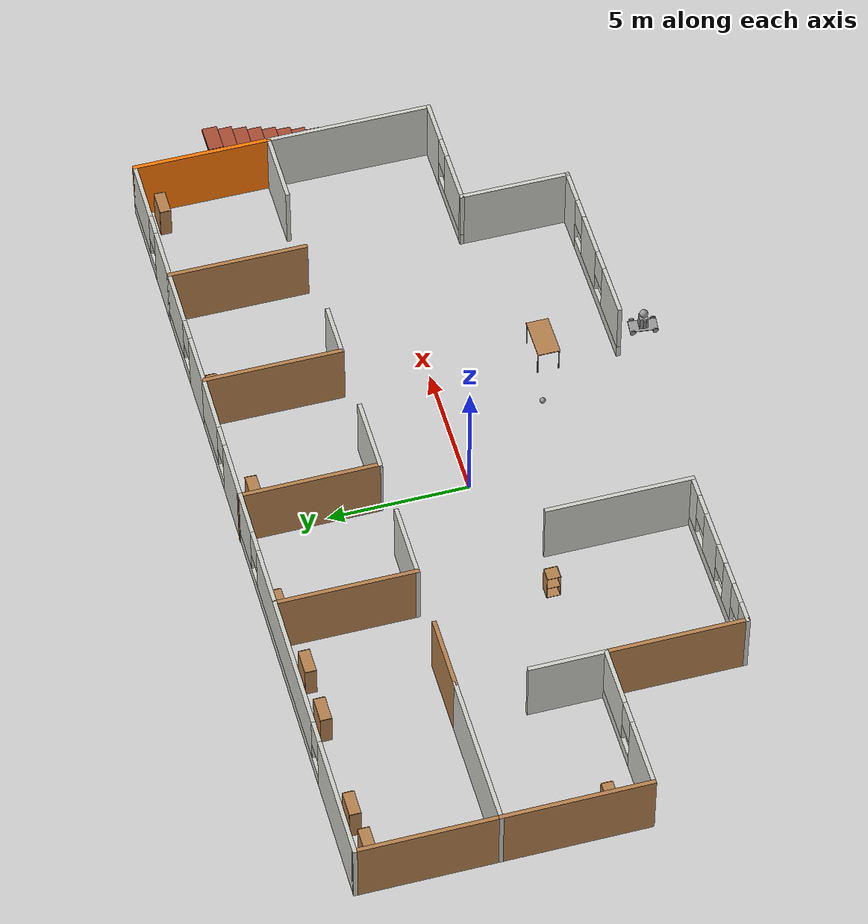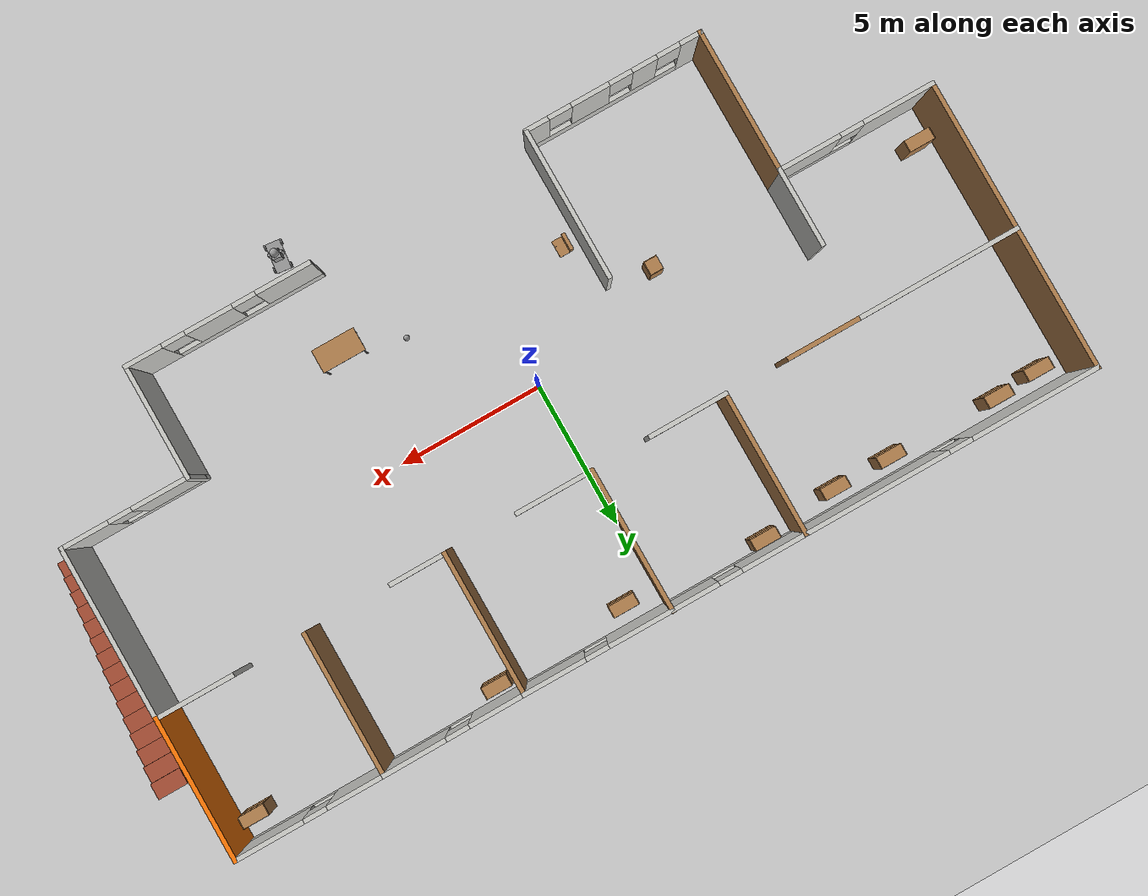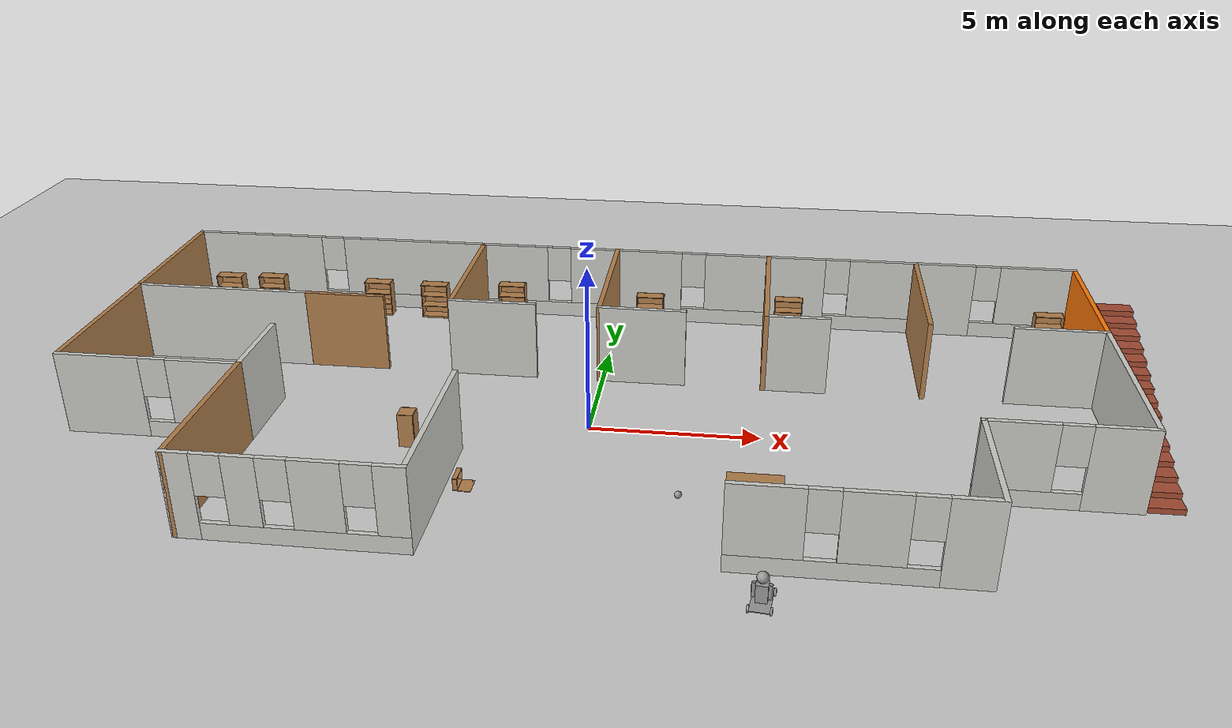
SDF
<sdf version="1.6">
 <world name="default">
  <plugin name="hello" filename="libhello.so"/>
  <light name="sun" type="directional">
   <pose>0 0 10 0 -0 0</pose>
   <diffuse>0.8 0.8 0.8 1</diffuse>
   <specular>0.2 0.2 0.2 1</specular>
   <attenuation>
    <range>1000</range>
    <constant>0.9</constant>
    <linear>0.01</linear>
    <quadratic>0.001</quadratic>
   </attenuation>
   <direction>-0.5 0.1 -0.9</direction>
  </light>
  <model name="ground_plane">
   <static>1</static>
   <link name="link">
    <collision name="collision">
     <geometry><plane><normal>0 0 1</normal><size>100 100</size></plane></geometry>
     <surface>
      <contact><collide_bitmask>65535</collide_bitmask></contact>
      <friction><ode><mu>100</mu><mu2>50</mu2></ode></friction>
     </surface>
    </collision>
    <visual name="visual">
     <cast_shadows>0</cast_shadows>
     <geometry><plane><normal>0 0 1</normal><size>100 100</size></plane></geometry>
     <material>
      <script><uri>file://media/materials/scripts/gazebo.material</uri><name>Gazebo/Grey</name></script>
     </material>
    </visual>
   </link>
  </model>
  <gravity>0 0 -9.8</gravity>
  <magnetic_field>6e-06 2.3e-05 -4.2e-05</magnetic_field>
  <atmosphere type="adiabatic"/>
  <physics name="default_physics" default="0" type="ode">
   <max_step_size>0.001</max_step_size>
   <real_time_factor>1</real_time_factor>
   <real_time_update_rate>1000</real_time_update_rate>
  </physics>
  <scene><ambient>0.4 0.4 0.4 1</ambient><background>0.7 0.7 0.7 1</background><shadows>1</shadows></scene>
  <audio><device>default</device></audio>
  <spherical_coordinates>
   <surface_model>EARTH_WGS84</surface_model>
   <latitude_deg>0</latitude_deg>
   <longitude_deg>0</longitude_deg>
   <elevation>0</elevation>
   <heading_deg>0</heading_deg>
  </spherical_coordinates>
  <model name="Building">
   <pose>0.521906 0.614781 0 0 -0 0</pose>
   <link name="Stairs_0">
    <visual name="Stairs_0_Visual_0">
     <pose>15.0099 -3.00809 0.083333 0 -0 -3.14159</pose>
     <geometry><box><size>1 0.530862 0.166667</size></box></geometry>
     <material>
      <script><uri>file://media/materials/scripts/gazebo.material</uri><name>Gazebo/Bricks</name></script>
      <ambient>0.760784 0.662745 0.627451 1</ambient>
     </material>
     <meta><layer>0</layer></meta>
    </visual>
    <collision name="Stairs_0_Collision_0">
     <geometry><box><size>1 0.530862 0.166667</size></box></geometry>
     <pose>15.0099 -3.00809 0.083333 0 -0 -3.14159</pose>
    </collision>
    <visual name="Stairs_0_Visual_1">
     <pose>15.0099 -2.47723 0.25 0 -0 -3.14159</pose>
     <geometry><box><size>1 0.530862 0.166667</size></box></geometry>
     <material>
      <script><uri>file://media/materials/scripts/gazebo.material</uri><name>Gazebo/Bricks</name></script>
      <ambient>0.760784 0.662745 0.627451 1</ambient>
     </material>
     <meta><layer>0</layer></meta>
    </visual>
    <collision name="Stairs_0_Collision_1">
     <geometry><box><size>1 0.530862 0.166667</size></box></geometry>
     <pose>15.0099 -2.47723 0.25 0 -0 -3.14159</pose>
    </collision>
    <visual name="Stairs_0_Visual_2">
     <pose>15.0099 -1.94637 0.416667 0 -0 -3.14159</pose>
     <geometry><box><size>1 0.530862 0.166667</size></box></geometry>
     <material>
      <script><uri>file://media/materials/scripts/gazebo.material</uri><name>Gazebo/Bricks</name></script>
      <ambient>0.760784 0.662745 0.627451 1</ambient>
     </material>
     <meta><layer>0</layer></meta>
    </visual>
    <collision name="Stairs_0_Collision_2">
     <geometry><box><size>1 0.530862 0.166667</size></box></geometry>
     <pose>15.0099 -1.94637 0.416667 0 -0 -3.14159</pose>
    </collision>
    <visual name="Stairs_0_Visual_3">
     <pose>15.0099 -1.41551 0.583333 0 -0 -3.14159</pose>
     <geometry><box><size>1 0.530862 0.166667</size></box></geometry>
     <material>
      <script><uri>file://media/materials/scripts/gazebo.material</uri><name>Gazebo/Bricks</name></script>
      <ambient>0.760784 0.662745 0.627451 1</ambient>
     </material>
     <meta><layer>0</layer></meta>
    </visual>
    <collision name="Stairs_0_Collision_3">
     <geometry><box><size>1 0.530862 0.166667</size></box></geometry>
     <pose>15.0099 -1.41551 0.583333 0 -0 -3.14159</pose>
    </collision>
    <visual name="Stairs_0_Visual_4">
     <pose>15.0099 -0.884647 0.75 0 -0 -3.14159</pose>
     <geometry><box><size>1 0.530862 0.166667</size></box></geometry>
     <material>
      <script><uri>file://media/materials/scripts/gazebo.material</uri><name>Gazebo/Bricks</name></script>
      <ambient>0.760784 0.662745 0.627451 1</ambient>
     </material>
     <meta><layer>0</layer></meta>
    </visual>
    <collision name="Stairs_0_Collision_4">
     <geometry><box><size>1 0.530862 0.166667</size></box></geometry>
     <pose>15.0099 -0.884647 0.75 0 -0 -3.14159</pose>
    </collision>
    <visual name="Stairs_0_Visual_5">
     <pose>15.0099 -0.353786 0.916667 0 -0 -3.14159</pose>
     <geometry><box><size>1 0.530862 0.166667</size></box></geometry>
     <material>
      <script><uri>file://media/materials/scripts/gazebo.material</uri><name>Gazebo/Bricks</name></script>
      <ambient>0.760784 0.662745 0.627451 1</ambient>
     </material>
     <meta><layer>0</layer></meta>
    </visual>
    <collision name="Stairs_0_Collision_5">
     <geometry><box><size>1 0.530862 0.166667</size></box></geometry>
     <pose>15.0099 -0.353786 0.916667 0 -0 -3.14159</pose>
    </collision>
    <visual name="Stairs_0_Visual_6">
     <pose>15.0099 0.177076 1.08333 0 -0 -3.14159</pose>
     <geometry><box><size>1 0.530862 0.166667</size></box></geometry>
     <material>
      <script><uri>file://media/materials/scripts/gazebo.material</uri><name>Gazebo/Bricks</name></script>
      <ambient>0.760784 0.662745 0.627451 1</ambient>
     </material>
     <meta><layer>0</layer></meta>
    </visual>
    <collision name="Stairs_0_Collision_6">
     <geometry><box><size>1 0.530862 0.166667</size></box></geometry>
     <pose>15.0099 0.177076 1.08333 0 -0 -3.14159</pose>
    </collision>
    <visual name="Stairs_0_Visual_7">
     <pose>15.0099 0.707938 1.25 0 -0 -3.14159</pose>
     <geometry><box><size>1 0.530862 0.166667</size></box></geometry>
     <material>
      <script><uri>file://media/materials/scripts/gazebo.material</uri><name>Gazebo/Bricks</name></script>
      <ambient>0.760784 0.662745 0.627451 1</ambient>
     </material>
     <meta><layer>0</layer></meta>
    </visual>
    <collision name="Stairs_0_Collision_7">
     <geometry><box><size>1 0.530862 0.166667</size></box></geometry>
     <pose>15.0099 0.707938 1.25 0 -0 -3.14159</pose>
    </collision>
    <visual name="Stairs_0_Visual_8">
     <pose>15.0099 1.2388 1.41667 0 -0 -3.14159</pose>
     <geometry><box><size>1 0.530862 0.166667</size></box></geometry>
     <material>
      <script><uri>file://media/materials/scripts/gazebo.material</uri><name>Gazebo/Bricks</name></script>
      <ambient>0.760784 0.662745 0.627451 1</ambient>
     </material>
     <meta><layer>0</layer></meta>
    </visual>
    <collision name="Stairs_0_Collision_8">
     <geometry><box><size>1 0.530862 0.166667</size></box></geometry>
     <pose>15.0099 1.2388 1.41667 0 -0 -3.14159</pose>
    </collision>
    <visual name="Stairs_0_Visual_9">
     <pose>15.0099 1.76966 1.58333 0 -0 -3.14159</pose>
     <geometry><box><size>1 0.530862 0.166667</size></box></geometry>
     <material>
      <script><uri>file://media/materials/scripts/gazebo.material</uri><name>Gazebo/Bricks</name></script>
      <ambient>0.760784 0.662745 0.627451 1</ambient>
     </material>
     <meta><layer>0</layer></meta>
    </visual>
    <collision name="Stairs_0_Collision_9">
     <geometry><box><size>1 0.530862 0.166667</size></box></geometry>
     <pose>15.0099 1.76966 1.58333 0 -0 -3.14159</pose>
    </collision>
    <visual name="Stairs_0_Visual_10">
     <pose>15.0099 2.30052 1.75 0 -0 -3.14159</pose>
     <geometry><box><size>1 0.530862 0.166667</size></box></geometry>
     <material>
      <script><uri>file://media/materials/scripts/gazebo.material</uri><name>Gazebo/Bricks</name></script>
      <ambient>0.760784 0.662745 0.627451 1</ambient>
     </material>
     <meta><layer>0</layer></meta>
    </visual>
    <collision name="Stairs_0_Collision_10">
     <geometry><box><size>1 0.530862 0.166667</size></box></geometry>
     <pose>15.0099 2.30052 1.75 0 -0 -3.14159</pose>
    </collision>
    <visual name="Stairs_0_Visual_11">
     <pose>15.0099 2.83139 1.91667 0 -0 -3.14159</pose>
     <geometry><box><size>1 0.530862 0.166667</size></box></geometry>
     <material>
      <script><uri>file://media/materials/scripts/gazebo.material</uri><name>Gazebo/Bricks</name></script>
      <ambient>0.760784 0.662745 0.627451 1</ambient>
     </material>
     <meta><layer>0</layer></meta>
    </visual>
    <collision name="Stairs_0_Collision_11">
     <geometry><box><size>1 0.530862 0.166667</size></box></geometry>
     <pose>15.0099 2.83139 1.91667 0 -0 -3.14159</pose>
    </collision>
    <visual name="Stairs_0_Visual_12">
     <pose>15.0099 3.36225 2.08333 0 -0 -3.14159</pose>
     <geometry><box><size>1 0.530862 0.166667</size></box></geometry>
     <material>
      <script><uri>file://media/materials/scripts/gazebo.material</uri><name>Gazebo/Bricks</name></script>
      <ambient>0.760784 0.662745 0.627451 1</ambient>
     </material>
     <meta><layer>0</layer></meta>
    </visual>
    <collision name="Stairs_0_Collision_12">
     <geometry><box><size>1 0.530862 0.166667</size></box></geometry>
     <pose>15.0099 3.36225 2.08333 0 -0 -3.14159</pose>
    </collision>
    <visual name="Stairs_0_Visual_13">
     <pose>15.0099 3.89311 2.25 0 -0 -3.14159</pose>
     <geometry><box><size>1 0.530862 0.166667</size></box></geometry>
     <material>
      <script><uri>file://media/materials/scripts/gazebo.material</uri><name>Gazebo/Bricks</name></script>
      <ambient>0.760784 0.662745 0.627451 1</ambient>
     </material>
     <meta><layer>0</layer></meta>
    </visual>
    <collision name="Stairs_0_Collision_13">
     <geometry><box><size>1 0.530862 0.166667</size></box></geometry>
     <pose>15.0099 3.89311 2.25 0 -0 -3.14159</pose>
    </collision>
    <visual name="Stairs_0_Visual_14">
     <pose>15.0099 4.42397 2.41667 0 -0 -3.14159</pose>
     <geometry><box><size>1 0.530862 0.166667</size></box></geometry>
     <material>
      <script><uri>file://media/materials/scripts/gazebo.material</uri><name>Gazebo/Bricks</name></script>
      <ambient>0.760784 0.662745 0.627451 1</ambient>
     </material>
     <meta><layer>0</layer></meta>
    </visual>
    <collision name="Stairs_0_Collision_14">
     <geometry><box><size>1 0.530862 0.166667</size></box></geometry>
     <pose>15.0099 4.42397 2.41667 0 -0 -3.14159</pose>
    </collision>
   </link>
   <link name="Wall_10">
    <collision name="Wall_10_Collision">
     <geometry><box><size>5.01454 0.15 2.5</size></box></geometry>
     <pose>0 0 1.25 0 -0 0</pose>
    </collision>
    <visual name="Wall_10_Visual">
     <pose>0 0 1.25 0 -0 0</pose>
     <geometry><box><size>5.01454 0.15 2.5</size></box></geometry>
     <material>
      <script><uri>file://media/materials/scripts/gazebo.material</uri><name>Gazebo/Wood</name></script>
      <ambient>1 1 1 1</ambient>
     </material>
     <meta><layer>0</layer></meta>
    </visual>
    <pose>-0.636839 4.97487 0 0 -0 -1.56723</pose>
   </link>
   <link name="Wall_12">
    <pose>1.91233 7.37959 0 0 -0 -0.002835</pose>
    <visual name="Wall_12_Visual_0">
     <pose>-1.49665 0 1.25 0 -0 0</pose>
     <geometry><box><size>2.2724 0.15 2.5</size></box></geometry>
     <material>
      <script><uri>file://media/materials/scripts/gazebo.material</uri><name>Gazebo/CeilingTiled</name></script>
      <ambient>0.996078 0.47451 0.0196078 1</ambient>
     </material>
     <meta><layer>0</layer></meta>
    </visual>
    <collision name="Wall_12_Collision_0">
     <geometry><box><size>2.2724 0.15 2.5</size></box></geometry>
     <pose>-1.49665 0 1.25 0 -0 0</pose>
    </collision>
    <visual name="Wall_12_Visual_1">
     <pose>1.1362 0 0.25 0 -0 0</pose>
     <geometry><box><size>2.99329 0.15 0.5</size></box></geometry>
     <material>
      <script><uri>file://media/materials/scripts/gazebo.material</uri><name>Gazebo/CeilingTiled</name></script>
      <ambient>0.996078 0.47451 0.0196078 1</ambient>
     </material>
     <meta><layer>0</layer></meta>
    </visual>
    <collision name="Wall_12_Collision_1">
     <geometry><box><size>2.99329 0.15 0.5</size></box></geometry>
     <pose>1.1362 0 0.25 0 -0 0</pose>
    </collision>
    <visual name="Wall_12_Visual_2">
     <pose>1.5362 0 1.5 0 -0 0</pose>
     <geometry><box><size>2.19329 0.15 2</size></box></geometry>
     <material>
      <script><uri>file://media/materials/scripts/gazebo.material</uri><name>Gazebo/CeilingTiled</name></script>
      <ambient>0.996078 0.47451 0.0196078 1</ambient>
     </material>
     <meta><layer>0</layer></meta>
    </visual>
    <collision name="Wall_12_Collision_2">
     <geometry><box><size>2.19329 0.15 2</size></box></geometry>
     <pose>1.5362 0 1.5 0 -0 0</pose>
    </collision>
    <visual name="Wall_12_Visual_3">
     <pose>0.039557 0 1.9 0 -0 0</pose>
     <geometry><box><size>0.8 0.15 1.2</size></box></geometry>
     <material>
      <script><uri>file://media/materials/scripts/gazebo.material</uri><name>Gazebo/CeilingTiled</name></script>
      <ambient>0.996078 0.47451 0.0196078 1</ambient>
     </material>
     <meta><layer>0</layer></meta>
    </visual>
    <collision name="Wall_12_Collision_3">
     <geometry><box><size>0.8 0.15 1.2</size></box></geometry>
     <pose>0.039557 0 1.9 0 -0 0</pose>
    </collision>
   </link>
   <link name="Wall_15">
    <pose>6.89267 7.38248 0 0 -0 0.004185</pose>
    <visual name="Wall_15_Visual_0">
     <pose>-1.50763 0 1.25 0 -0 0</pose>
     <geometry><box><size>1.97978 0.15 2.5</size></box></geometry>
     <material>
      <script><uri>file://media/materials/scripts/gazebo.material</uri><name>Gazebo/CeilingTiled</name></script>
      <ambient>0.435294 0.796078 0.67451 1</ambient>
     </material>
     <meta><layer>0</layer></meta>
    </visual>
    <collision name="Wall_15_Collision_0">
     <geometry><box><size>1.97978 0.15 2.5</size></box></geometry>
     <pose>-1.50763 0 1.25 0 -0 0</pose>
    </collision>
    <visual name="Wall_15_Visual_1">
     <pose>0.989888 0 0.25 0 -0 0</pose>
     <geometry><box><size>3.01526 0.15 0.5</size></box></geometry>
     <material>
      <script><uri>file://media/materials/scripts/gazebo.material</uri><name>Gazebo/CeilingTiled</name></script>
      <ambient>0.435294 0.796078 0.67451 1</ambient>
     </material>
     <meta><layer>0</layer></meta>
    </visual>
    <collision name="Wall_15_Collision_1">
     <geometry><box><size>3.01526 0.15 0.5</size></box></geometry>
     <pose>0.989888 0 0.25 0 -0 0</pose>
    </collision>
    <visual name="Wall_15_Visual_2">
     <pose>1.38989 0 1.5 0 -0 0</pose>
     <geometry><box><size>2.21526 0.15 2</size></box></geometry>
     <material>
      <script><uri>file://media/materials/scripts/gazebo.material</uri><name>Gazebo/CeilingTiled</name></script>
      <ambient>0.435294 0.796078 0.67451 1</ambient>
     </material>
     <meta><layer>0</layer></meta>
    </visual>
    <collision name="Wall_15_Collision_2">
     <geometry><box><size>2.21526 0.15 2</size></box></geometry>
     <pose>1.38989 0 1.5 0 -0 0</pose>
    </collision>
    <visual name="Wall_15_Visual_3">
     <pose>-0.117741 0 1.9 0 -0 0</pose>
     <geometry><box><size>0.8 0.15 1.2</size></box></geometry>
     <material>
      <script><uri>file://media/materials/scripts/gazebo.material</uri><name>Gazebo/CeilingTiled</name></script>
      <ambient>0.435294 0.796078 0.67451 1</ambient>
     </material>
     <meta><layer>0</layer></meta>
    </visual>
    <collision name="Wall_15_Collision_3">
     <geometry><box><size>0.8 0.15 1.2</size></box></geometry>
     <pose>-0.117741 0 1.9 0 -0 0</pose>
    </collision>
   </link>
   <link name="Wall_16">
    <collision name="Wall_16_Collision">
     <geometry><box><size>5 0.15 2.5</size></box></geometry>
     <pose>0 0 1.25 0 -0 0</pose>
    </collision>
    <visual name="Wall_16_Visual">
     <pose>0 0 1.25 0 -0 0</pose>
     <geometry><box><size>5 0.15 2.5</size></box></geometry>
     <material>
      <script><uri>file://media/materials/scripts/gazebo.material</uri><name>Gazebo/Wood</name></script>
      <ambient>1 1 1 1</ambient>
     </material>
     <meta><layer>0</layer></meta>
    </visual>
    <pose>9.31516 4.96762 0 0 -0 -1.5708</pose>
   </link>
   <link name="Wall_18">
    <collision name="Wall_18_Collision">
     <geometry><box><size>5.57093 0.15 2.5</size></box></geometry>
     <pose>0 0 1.25 0 -0 0</pose>
    </collision>
    <visual name="Wall_18_Visual">
     <pose>0 0 1.25 0 -0 0</pose>
     <geometry><box><size>5.57093 0.15 2.5</size></box></geometry>
     <material>
      <script><uri>file://media/materials/scripts/gazebo.material</uri><name>Gazebo/CeilingTiled</name></script>
      <ambient>0.435294 0.796078 0.67451 1</ambient>
     </material>
     <meta><layer>0</layer></meta>
    </visual>
    <pose>-12.7244 2.54262 0 0 -0 3.14159</pose>
   </link>
   <link name="Wall_20">
    <collision name="Wall_20_Collision">
     <geometry><box><size>5.25 0.15 2.5</size></box></geometry>
     <pose>0 0 1.25 0 -0 0</pose>
    </collision>
    <visual name="Wall_20_Visual">
     <pose>0 0 1.25 0 -0 0</pose>
     <geometry><box><size>5.25 0.15 2.5</size></box></geometry>
     <material>
      <script><uri>file://media/materials/scripts/gazebo.material</uri><name>Gazebo/Wood</name></script>
      <ambient>1 1 1 1</ambient>
     </material>
     <meta><layer>0</layer></meta>
    </visual>
    <pose>-15.4348 -0.007385 0 0 -0 -1.5708</pose>
   </link>
   <link name="Wall_21">
    <pose>-12.7598 -2.55739 0 0 -0 0</pose>
    <visual name="Wall_21_Visual_0">
     <pose>-1.50027 0 1.25 0 -0 0</pose>
     <geometry><box><size>2.49946 0.15 2.5</size></box></geometry>
     <material>
      <script><uri>file://media/materials/scripts/gazebo.material</uri><name>Gazebo/CeilingTiled</name></script>
      <ambient>0.921569 0.807843 0.615686 1</ambient>
     </material>
     <meta><layer>0</layer></meta>
    </visual>
    <collision name="Wall_21_Collision_0">
     <geometry><box><size>2.49946 0.15 2.5</size></box></geometry>
     <pose>-1.50027 0 1.25 0 -0 0</pose>
    </collision>
    <visual name="Wall_21_Visual_1">
     <pose>1.24973 0 0.25 0 -0 0</pose>
     <geometry><box><size>3.00054 0.15 0.5</size></box></geometry>
     <material>
      <script><uri>file://media/materials/scripts/gazebo.material</uri><name>Gazebo/CeilingTiled</name></script>
      <ambient>0.921569 0.807843 0.615686 1</ambient>
     </material>
     <meta><layer>0</layer></meta>
    </visual>
    <collision name="Wall_21_Collision_1">
     <geometry><box><size>3.00054 0.15 0.5</size></box></geometry>
     <pose>1.24973 0 0.25 0 -0 0</pose>
    </collision>
    <visual name="Wall_21_Visual_2">
     <pose>1.64973 0 1.5 0 -0 0</pose>
     <geometry><box><size>2.20054 0.15 2</size></box></geometry>
     <material>
      <script><uri>file://media/materials/scripts/gazebo.material</uri><name>Gazebo/CeilingTiled</name></script>
      <ambient>0.921569 0.807843 0.615686 1</ambient>
     </material>
     <meta><layer>0</layer></meta>
    </visual>
    <collision name="Wall_21_Collision_2">
     <geometry><box><size>2.20054 0.15 2</size></box></geometry>
     <pose>1.64973 0 1.5 0 -0 0</pose>
    </collision>
    <visual name="Wall_21_Visual_3">
     <pose>0.149458 0 1.9 0 -0 0</pose>
     <geometry><box><size>0.8 0.15 1.2</size></box></geometry>
     <material>
      <script><uri>file://media/materials/scripts/gazebo.material</uri><name>Gazebo/CeilingTiled</name></script>
      <ambient>0.921569 0.807843 0.615686 1</ambient>
     </material>
     <meta><layer>0</layer></meta>
    </visual>
    <collision name="Wall_21_Collision_3">
     <geometry><box><size>0.8 0.15 1.2</size></box></geometry>
     <pose>0.149458 0 1.9 0 -0 0</pose>
    </collision>
   </link>
   <link name="Wall_22">
    <collision name="Wall_22_Collision">
     <geometry><box><size>5 0.15 2.5</size></box></geometry>
     <pose>0 0 1.25 0 -0 0</pose>
    </collision>
    <visual name="Wall_22_Visual">
     <pose>0 0 1.25 0 -0 0</pose>
     <geometry><box><size>5 0.15 2.5</size></box></geometry>
     <material>
      <script><uri>file://media/materials/scripts/gazebo.material</uri><name>Gazebo/Wood</name></script>
      <ambient>1 1 1 1</ambient>
     </material>
     <meta><layer>0</layer></meta>
    </visual>
    <pose>-10.0848 -4.98238 0 0 -0 -1.5708</pose>
   </link>
   <link name="Wall_23">
    <pose>-7.03484 -7.40738 0 0 -0 0</pose>
    <visual name="Wall_23_Visual_0">
     <pose>-2.72612 0 1.25 0 -0 0</pose>
     <geometry><box><size>0.797767 0.15 2.5</size></box></geometry>
     <material>
      <script><uri>file://media/materials/scripts/gazebo.material</uri><name>Gazebo/CeilingTiled</name></script>
      <ambient>0.921569 0.807843 0.615686 1</ambient>
     </material>
     <meta><layer>0</layer></meta>
    </visual>
    <collision name="Wall_23_Collision_0">
     <geometry><box><size>0.797767 0.15 2.5</size></box></geometry>
     <pose>-2.72612 0 1.25 0 -0 0</pose>
    </collision>
    <visual name="Wall_23_Visual_1">
     <pose>0.398883 0 0.25 0 -0 0</pose>
     <geometry><box><size>5.45223 0.15 0.5</size></box></geometry>
     <material>
      <script><uri>file://media/materials/scripts/gazebo.material</uri><name>Gazebo/CeilingTiled</name></script>
      <ambient>0.921569 0.807843 0.615686 1</ambient>
     </material>
     <meta><layer>0</layer></meta>
    </visual>
    <collision name="Wall_23_Collision_1">
     <geometry><box><size>5.45223 0.15 0.5</size></box></geometry>
     <pose>0.398883 0 0.25 0 -0 0</pose>
    </collision>
    <visual name="Wall_23_Visual_2">
     <pose>-1.09245 0 1.5 0 -0 0</pose>
     <geometry><box><size>0.869566 0.15 2</size></box></geometry>
     <material>
      <script><uri>file://media/materials/scripts/gazebo.material</uri><name>Gazebo/CeilingTiled</name></script>
      <ambient>0.921569 0.807843 0.615686 1</ambient>
     </material>
     <meta><layer>0</layer></meta>
    </visual>
    <collision name="Wall_23_Collision_2">
     <geometry><box><size>0.869566 0.15 2</size></box></geometry>
     <pose>-1.09245 0 1.5 0 -0 0</pose>
    </collision>
    <visual name="Wall_23_Visual_3">
     <pose>0.808999 0 1.5 0 -0 0</pose>
     <geometry><box><size>1.33333 0.15 2</size></box></geometry>
     <material>
      <script><uri>file://media/materials/scripts/gazebo.material</uri><name>Gazebo/CeilingTiled</name></script>
      <ambient>0.921569 0.807843 0.615686 1</ambient>
     </material>
     <meta><layer>0</layer></meta>
    </visual>
    <collision name="Wall_23_Collision_3">
     <geometry><box><size>1.33333 0.15 2</size></box></geometry>
     <pose>0.808999 0 1.5 0 -0 0</pose>
    </collision>
    <visual name="Wall_23_Visual_4">
     <pose>2.70033 0 1.5 0 -0 0</pose>
     <geometry><box><size>0.849334 0.15 2</size></box></geometry>
     <material>
      <script><uri>file://media/materials/scripts/gazebo.material</uri><name>Gazebo/CeilingTiled</name></script>
      <ambient>0.921569 0.807843 0.615686 1</ambient>
     </material>
     <meta><layer>0</layer></meta>
    </visual>
    <collision name="Wall_23_Collision_4">
     <geometry><box><size>0.849334 0.15 2</size></box></geometry>
     <pose>2.70033 0 1.5 0 -0 0</pose>
    </collision>
    <visual name="Wall_23_Visual_5">
     <pose>-1.92723 0 1.9 0 -0 0</pose>
     <geometry><box><size>0.8 0.15 1.2</size></box></geometry>
     <material>
      <script><uri>file://media/materials/scripts/gazebo.material</uri><name>Gazebo/CeilingTiled</name></script>
      <ambient>0.921569 0.807843 0.615686 1</ambient>
     </material>
     <meta><layer>0</layer></meta>
    </visual>
    <collision name="Wall_23_Collision_5">
     <geometry><box><size>0.8 0.15 1.2</size></box></geometry>
     <pose>-1.92723 0 1.9 0 -0 0</pose>
    </collision>
    <visual name="Wall_23_Visual_6">
     <pose>-0.257668 0 1.9 0 -0 0</pose>
     <geometry><box><size>0.8 0.15 1.2</size></box></geometry>
     <material>
      <script><uri>file://media/materials/scripts/gazebo.material</uri><name>Gazebo/CeilingTiled</name></script>
      <ambient>0.921569 0.807843 0.615686 1</ambient>
     </material>
     <meta><layer>0</layer></meta>
    </visual>
    <collision name="Wall_23_Collision_6">
     <geometry><box><size>0.8 0.15 1.2</size></box></geometry>
     <pose>-0.257668 0 1.9 0 -0 0</pose>
    </collision>
    <visual name="Wall_23_Visual_7">
     <pose>1.87567 0 1.9 0 -0 0</pose>
     <geometry><box><size>0.8 0.15 1.2</size></box></geometry>
     <material>
      <script><uri>file://media/materials/scripts/gazebo.material</uri><name>Gazebo/CeilingTiled</name></script>
      <ambient>0.921569 0.807843 0.615686 1</ambient>
     </material>
     <meta><layer>0</layer></meta>
    </visual>
    <collision name="Wall_23_Collision_7">
     <geometry><box><size>0.8 0.15 1.2</size></box></geometry>
     <pose>1.87567 0 1.9 0 -0 0</pose>
    </collision>
   </link>
   <link name="Wall_24">
    <collision name="Wall_24_Collision">
     <geometry><box><size>5.25 0.15 2.5</size></box></geometry>
     <pose>0 0 1.25 0 -0 0</pose>
    </collision>
    <visual name="Wall_24_Visual">
     <pose>0 0 1.25 0 -0 0</pose>
     <geometry><box><size>5.25 0.15 2.5</size></box></geometry>
     <material>
      <script><uri>file://media/materials/scripts/gazebo.material</uri><name>Gazebo/CeilingTiled</name></script>
      <ambient>1 0.764706 0.305882 1</ambient>
     </material>
     <meta><layer>0</layer></meta>
    </visual>
    <pose>-3.98484 -4.85738 0 0 -0 1.5708</pose>
   </link>
   <link name="Wall_28">
    <collision name="Wall_28_Collision">
     <geometry><box><size>6 0.15 2.5</size></box></geometry>
     <pose>0 0 1.25 0 -0 0</pose>
    </collision>
    <visual name="Wall_28_Visual">
     <pose>0 0 1.25 0 -0 0</pose>
     <geometry><box><size>6 0.15 2.5</size></box></geometry>
     <material>
      <script><uri>file://media/materials/scripts/gazebo.material</uri><name>Gazebo/CeilingTiled</name></script>
      <ambient>0.435294 0.796078 0.67451 1</ambient>
     </material>
     <meta><layer>0</layer></meta>
    </visual>
    <pose>14.4152 -0.382385 0 0 -0 -1.5708</pose>
   </link>
   <link name="Wall_29">
    <pose>12.2402 -3.30739 0 0 -0 3.14159</pose>
    <visual name="Wall_29_Visual_0">
     <pose>-1.40601 0 1.25 0 -0 0</pose>
     <geometry><box><size>1.68798 0.15 2.5</size></box></geometry>
     <material>
      <script><uri>file://media/materials/scripts/gazebo.material</uri><name>Gazebo/CeilingTiled</name></script>
      <ambient>0.921569 0.807843 0.615686 1</ambient>
     </material>
     <meta><layer>0</layer></meta>
    </visual>
    <collision name="Wall_29_Collision_0">
     <geometry><box><size>1.68798 0.15 2.5</size></box></geometry>
     <pose>-1.40601 0 1.25 0 -0 0</pose>
    </collision>
    <visual name="Wall_29_Visual_1">
     <pose>0.843991 0 0.25 0 -0 0</pose>
     <geometry><box><size>2.81202 0.15 0.5</size></box></geometry>
     <material>
      <script><uri>file://media/materials/scripts/gazebo.material</uri><name>Gazebo/CeilingTiled</name></script>
      <ambient>0.921569 0.807843 0.615686 1</ambient>
     </material>
     <meta><layer>0</layer></meta>
    </visual>
    <collision name="Wall_29_Collision_1">
     <geometry><box><size>2.81202 0.15 0.5</size></box></geometry>
     <pose>0.843991 0 0.25 0 -0 0</pose>
    </collision>
    <visual name="Wall_29_Visual_2">
     <pose>1.24399 0 1.5 0 -0 0</pose>
     <geometry><box><size>2.01202 0.15 2</size></box></geometry>
     <material>
      <script><uri>file://media/materials/scripts/gazebo.material</uri><name>Gazebo/CeilingTiled</name></script>
      <ambient>0.921569 0.807843 0.615686 1</ambient>
     </material>
     <meta><layer>0</layer></meta>
    </visual>
    <collision name="Wall_29_Collision_2">
     <geometry><box><size>2.01202 0.15 2</size></box></geometry>
     <pose>1.24399 0 1.5 0 -0 0</pose>
    </collision>
    <visual name="Wall_29_Visual_3">
     <pose>-0.162018 0 1.9 0 -0 0</pose>
     <geometry><box><size>0.8 0.15 1.2</size></box></geometry>
     <material>
      <script><uri>file://media/materials/scripts/gazebo.material</uri><name>Gazebo/CeilingTiled</name></script>
      <ambient>0.921569 0.807843 0.615686 1</ambient>
     </material>
     <meta><layer>0</layer></meta>
    </visual>
    <collision name="Wall_29_Collision_3">
     <geometry><box><size>0.8 0.15 1.2</size></box></geometry>
     <pose>-0.162018 0 1.9 0 -0 0</pose>
    </collision>
   </link>
   <link name="Wall_30">
    <collision name="Wall_30_Collision">
     <geometry><box><size>4 0.15 2.5</size></box></geometry>
     <pose>0 0 1.25 0 -0 0</pose>
    </collision>
    <visual name="Wall_30_Visual">
     <pose>0 0 1.25 0 -0 0</pose>
     <geometry><box><size>4 0.15 2.5</size></box></geometry>
     <material>
      <script><uri>file://media/materials/scripts/gazebo.material</uri><name>Gazebo/CeilingTiled</name></script>
      <ambient>1 0.764706 0.305882 1</ambient>
     </material>
     <meta><layer>0</layer></meta>
    </visual>
    <pose>10.0652 -5.23238 0 0 -0 -1.5708</pose>
   </link>
   <link name="Wall_31">
    <pose>6.89016 -7.15738 0 0 -0 3.14159</pose>
    <visual name="Wall_31_Visual_0">
     <pose>-2.58681 0 1.25 0 -0 0</pose>
     <geometry><box><size>1.32639 0.15 2.5</size></box></geometry>
     <material>
      <script><uri>file://media/materials/scripts/gazebo.material</uri><name>Gazebo/CeilingTiled</name></script>
      <ambient>0.921569 0.807843 0.615686 1</ambient>
     </material>
     <meta><layer>0</layer></meta>
    </visual>
    <collision name="Wall_31_Collision_0">
     <geometry><box><size>1.32639 0.15 2.5</size></box></geometry>
     <pose>-2.58681 0 1.25 0 -0 0</pose>
    </collision>
    <visual name="Wall_31_Visual_1">
     <pose>0.663194 0 0.25 0 -0 0</pose>
     <geometry><box><size>5.17361 0.15 0.5</size></box></geometry>
     <material>
      <script><uri>file://media/materials/scripts/gazebo.material</uri><name>Gazebo/CeilingTiled</name></script>
      <ambient>0.921569 0.807843 0.615686 1</ambient>
     </material>
     <meta><layer>0</layer></meta>
    </visual>
    <collision name="Wall_31_Collision_1">
     <geometry><box><size>5.17361 0.15 0.5</size></box></geometry>
     <pose>0.663194 0 0.25 0 -0 0</pose>
    </collision>
    <visual name="Wall_31_Visual_2">
     <pose>-0.302357 0 1.5 0 -0 0</pose>
     <geometry><box><size>1.64251 0.15 2</size></box></geometry>
     <material>
      <script><uri>file://media/materials/scripts/gazebo.material</uri><name>Gazebo/CeilingTiled</name></script>
      <ambient>0.921569 0.807843 0.615686 1</ambient>
     </material>
     <meta><layer>0</layer></meta>
    </visual>
    <collision name="Wall_31_Collision_2">
     <geometry><box><size>1.64251 0.15 2</size></box></geometry>
     <pose>-0.302357 0 1.5 0 -0 0</pose>
    </collision>
    <visual name="Wall_31_Visual_3">
     <pose>2.28445 0 1.5 0 -0 0</pose>
     <geometry><box><size>1.9311 0.15 2</size></box></geometry>
     <material>
      <script><uri>file://media/materials/scripts/gazebo.material</uri><name>Gazebo/CeilingTiled</name></script>
      <ambient>0.921569 0.807843 0.615686 1</ambient>
     </material>
     <meta><layer>0</layer></meta>
    </visual>
    <collision name="Wall_31_Collision_3">
     <geometry><box><size>1.9311 0.15 2</size></box></geometry>
     <pose>2.28445 0 1.5 0 -0 0</pose>
    </collision>
    <visual name="Wall_31_Visual_4">
     <pose>-1.52361 0 1.9 0 -0 0</pose>
     <geometry><box><size>0.8 0.15 1.2</size></box></geometry>
     <material>
      <script><uri>file://media/materials/scripts/gazebo.material</uri><name>Gazebo/CeilingTiled</name></script>
      <ambient>0.921569 0.807843 0.615686 1</ambient>
     </material>
     <meta><layer>0</layer></meta>
    </visual>
    <collision name="Wall_31_Collision_4">
     <geometry><box><size>0.8 0.15 1.2</size></box></geometry>
     <pose>-1.52361 0 1.9 0 -0 0</pose>
    </collision>
    <visual name="Wall_31_Visual_5">
     <pose>0.9189 0 1.9 0 -0 0</pose>
     <geometry><box><size>0.8 0.15 1.2</size></box></geometry>
     <material>
      <script><uri>file://media/materials/scripts/gazebo.material</uri><name>Gazebo/CeilingTiled</name></script>
      <ambient>0.921569 0.807843 0.615686 1</ambient>
     </material>
     <meta><layer>0</layer></meta>
    </visual>
    <collision name="Wall_31_Collision_5">
     <geometry><box><size>0.8 0.15 1.2</size></box></geometry>
     <pose>0.9189 0 1.9 0 -0 0</pose>
    </collision>
   </link>
   <link name="Wall_35">
    <collision name="Wall_35_Collision">
     <geometry><box><size>2.67907 0.15 2.5</size></box></geometry>
     <pose>0 0 1.25 0 -0 0</pose>
    </collision>
    <visual name="Wall_35_Visual">
     <pose>0 0 1.25 0 -0 0</pose>
     <geometry><box><size>2.67907 0.15 2.5</size></box></geometry>
     <material>
      <script><uri>file://media/materials/scripts/gazebo.material</uri><name>Gazebo/Wood</name></script>
      <ambient>1 1 1 1</ambient>
     </material>
     <meta><layer>0</layer></meta>
    </visual>
    <pose>-8.74937 2.54262 0 0 -0 0</pose>
   </link>
   <link name="Wall_37">
    <collision name="Wall_37_Collision">
     <geometry><box><size>2.75 0.15 2.5</size></box></geometry>
     <pose>0 0 1.25 0 -0 0</pose>
    </collision>
    <visual name="Wall_37_Visual">
     <pose>0 0 1.25 0 -0 0</pose>
     <geometry><box><size>2.75 0.15 2.5</size></box></geometry>
     <material>
      <script><uri>file://media/materials/scripts/gazebo.material</uri><name>Gazebo/CeilingTiled</name></script>
      <ambient>0.996078 0.47451 0.0196078 1</ambient>
     </material>
     <meta><layer>0</layer></meta>
    </visual>
    <pose>-3.97539 2.52234 0 0 -0 0</pose>
   </link>
   <link name="Wall_39">
    <collision name="Wall_39_Collision">
     <geometry><box><size>2.75 0.15 2.5</size></box></geometry>
     <pose>0 0 1.25 0 -0 0</pose>
    </collision>
    <visual name="Wall_39_Visual">
     <pose>0 0 1.25 0 -0 0</pose>
     <geometry><box><size>2.75 0.15 2.5</size></box></geometry>
     <material>
      <script><uri>file://media/materials/scripts/gazebo.material</uri><name>Gazebo/CeilingTiled</name></script>
      <ambient>0.996078 0.47451 0.0196078 1</ambient>
     </material>
     <meta><layer>0</layer></meta>
    </visual>
    <pose>0.671822 2.54262 0 0 -0 0</pose>
   </link>
   <link name="Wall_41">
    <collision name="Wall_41_Collision">
     <geometry><box><size>5 0.15 2.5</size></box></geometry>
     <pose>0 0 1.25 0 -0 0</pose>
    </collision>
    <visual name="Wall_41_Visual">
     <pose>0 0 1.25 0 -0 0</pose>
     <geometry><box><size>5 0.15 2.5</size></box></geometry>
     <material>
      <script><uri>file://media/materials/scripts/gazebo.material</uri><name>Gazebo/Wood</name></script>
      <ambient>1 1 1 1</ambient>
     </material>
     <meta><layer>0</layer></meta>
    </visual>
    <pose>-15.4348 4.96762 0 0 -0 1.5708</pose>
   </link>
   <link name="Wall_42">
    <pose>-8.04017 7.38973 0 0 -0 -0.00039</pose>
    <visual name="Wall_42_Visual_0">
     <pose>-5.24521 0 1.25 0 -0 0</pose>
     <geometry><box><size>4.44893 0.15 2.5</size></box></geometry>
     <material>
      <script><uri>file://media/materials/scripts/gazebo.material</uri><name>Gazebo/CeilingTiled</name></script>
      <ambient>0.996078 0.47451 0.0196078 1</ambient>
     </material>
     <meta><layer>0</layer></meta>
    </visual>
    <collision name="Wall_42_Collision_0">
     <geometry><box><size>4.44893 0.15 2.5</size></box></geometry>
     <pose>-5.24521 0 1.25 0 -0 0</pose>
    </collision>
    <visual name="Wall_42_Visual_1">
     <pose>2.22446 0 0.25 0 -0 0</pose>
     <geometry><box><size>10.4904 0.15 0.5</size></box></geometry>
     <material>
      <script><uri>file://media/materials/scripts/gazebo.material</uri><name>Gazebo/CeilingTiled</name></script>
      <ambient>0.996078 0.47451 0.0196078 1</ambient>
     </material>
     <meta><layer>0</layer></meta>
    </visual>
    <collision name="Wall_42_Collision_1">
     <geometry><box><size>10.4904 0.15 0.5</size></box></geometry>
     <pose>2.22446 0 0.25 0 -0 0</pose>
    </collision>
    <visual name="Wall_42_Visual_2">
     <pose>1.38113 0 1.5 0 -0 0</pose>
     <geometry><box><size>7.20375 0.15 2</size></box></geometry>
     <material>
      <script><uri>file://media/materials/scripts/gazebo.material</uri><name>Gazebo/CeilingTiled</name></script>
      <ambient>0.996078 0.47451 0.0196078 1</ambient>
     </material>
     <meta><layer>0</layer></meta>
    </visual>
    <collision name="Wall_42_Collision_2">
     <geometry><box><size>7.20375 0.15 2</size></box></geometry>
     <pose>1.38113 0 1.5 0 -0 0</pose>
    </collision>
    <visual name="Wall_42_Visual_3">
     <pose>6.62634 0 1.5 0 -0 0</pose>
     <geometry><box><size>1.68666 0.15 2</size></box></geometry>
     <material>
      <script><uri>file://media/materials/scripts/gazebo.material</uri><name>Gazebo/CeilingTiled</name></script>
      <ambient>0.996078 0.47451 0.0196078 1</ambient>
     </material>
     <meta><layer>0</layer></meta>
    </visual>
    <collision name="Wall_42_Collision_3">
     <geometry><box><size>1.68666 0.15 2</size></box></geometry>
     <pose>6.62634 0 1.5 0 -0 0</pose>
    </collision>
    <visual name="Wall_42_Visual_4">
     <pose>-2.62074 0 1.9 0 -0 0</pose>
     <geometry><box><size>0.8 0.15 1.2</size></box></geometry>
     <material>
      <script><uri>file://media/materials/scripts/gazebo.material</uri><name>Gazebo/CeilingTiled</name></script>
      <ambient>0.996078 0.47451 0.0196078 1</ambient>
     </material>
     <meta><layer>0</layer></meta>
    </visual>
    <collision name="Wall_42_Collision_4">
     <geometry><box><size>0.8 0.15 1.2</size></box></geometry>
     <pose>-2.62074 0 1.9 0 -0 0</pose>
    </collision>
    <visual name="Wall_42_Visual_5">
     <pose>5.38301 0 1.9 0 -0 0</pose>
     <geometry><box><size>0.8 0.15 1.2</size></box></geometry>
     <material>
      <script><uri>file://media/materials/scripts/gazebo.material</uri><name>Gazebo/CeilingTiled</name></script>
      <ambient>0.996078 0.47451 0.0196078 1</ambient>
     </material>
     <meta><layer>0</layer></meta>
    </visual>
    <collision name="Wall_42_Collision_5">
     <geometry><box><size>0.8 0.15 1.2</size></box></geometry>
     <pose>5.38301 0 1.9 0 -0 0</pose>
    </collision>
   </link>
   <link name="Wall_44">
    <collision name="Wall_44_Collision">
     <geometry><box><size>5 0.15 2.5</size></box></geometry>
     <pose>0 0 1.25 0 -0 0</pose>
    </collision>
    <visual name="Wall_44_Visual">
     <pose>0 0 1.25 0 -0 0</pose>
     <geometry><box><size>5 0.15 2.5</size></box></geometry>
     <material>
      <script><uri>file://media/materials/scripts/gazebo.material</uri><name>Gazebo/Wood</name></script>
      <ambient>1 1 1 1</ambient>
     </material>
     <meta><layer>0</layer></meta>
    </visual>
    <pose>4.47017 4.94734 0 0 -0 -1.5708</pose>
   </link>
   <link name="Wall_45">
    <collision name="Wall_45_Collision">
     <geometry><box><size>2 0.15 2.5</size></box></geometry>
     <pose>0 0 1.25 0 -0 0</pose>
    </collision>
    <visual name="Wall_45_Visual">
     <pose>0 0 1.25 0 -0 0</pose>
     <geometry><box><size>2 0.15 2.5</size></box></geometry>
     <material>
      <script><uri>file://media/materials/scripts/gazebo.material</uri><name>Gazebo/CeilingTiled</name></script>
      <ambient>0.996078 0.47451 0.0196078 1</ambient>
     </material>
     <meta><layer>0</layer></meta>
    </visual>
    <pose>5.39517 2.52234 0 0 -0 0</pose>
   </link>
   <link name="Wall_47">
    <collision name="Wall_47_Collision">
     <geometry><box><size>5 0.15 2.5</size></box></geometry>
     <pose>0 0 1.25 0 -0 0</pose>
    </collision>
    <visual name="Wall_47_Visual">
     <pose>0 0 1.25 0 -0 0</pose>
     <geometry><box><size>5 0.15 2.5</size></box></geometry>
     <material>
      <script><uri>file://media/materials/scripts/gazebo.material</uri><name>Gazebo/Wood</name></script>
      <ambient>1 1 1 1</ambient>
     </material>
     <meta><layer>0</layer></meta>
    </visual>
    <pose>-5.27539 4.94734 0 0 -0 1.5708</pose>
   </link>
   <link name="Wall_49">
    <pose>11.8652 7.39262 0 0 -0 0</pose>
    <visual name="Wall_49_Visual_0">
     <pose>-1.60924 0 1.25 0 -0 0</pose>
     <geometry><box><size>2.03152 0.15 2.5</size></box></geometry>
     <material>
      <script><uri>file://media/materials/scripts/gazebo.material</uri><name>Gazebo/CeilingTiled</name></script>
      <ambient>0.996078 0.47451 0.0196078 1</ambient>
     </material>
     <meta><layer>0</layer></meta>
    </visual>
    <collision name="Wall_49_Collision_0">
     <geometry><box><size>2.03152 0.15 2.5</size></box></geometry>
     <pose>-1.60924 0 1.25 0 -0 0</pose>
    </collision>
    <visual name="Wall_49_Visual_1">
     <pose>1.01576 0 0.25 0 -0 0</pose>
     <geometry><box><size>3.21848 0.15 0.5</size></box></geometry>
     <material>
      <script><uri>file://media/materials/scripts/gazebo.material</uri><name>Gazebo/CeilingTiled</name></script>
      <ambient>0.996078 0.47451 0.0196078 1</ambient>
     </material>
     <meta><layer>0</layer></meta>
    </visual>
    <collision name="Wall_49_Collision_1">
     <geometry><box><size>3.21848 0.15 0.5</size></box></geometry>
     <pose>1.01576 0 0.25 0 -0 0</pose>
    </collision>
    <visual name="Wall_49_Visual_2">
     <pose>1.41576 0 1.5 0 -0 0</pose>
     <geometry><box><size>2.41848 0.15 2</size></box></geometry>
     <material>
      <script><uri>file://media/materials/scripts/gazebo.material</uri><name>Gazebo/CeilingTiled</name></script>
      <ambient>0.996078 0.47451 0.0196078 1</ambient>
     </material>
     <meta><layer>0</layer></meta>
    </visual>
    <collision name="Wall_49_Collision_2">
     <geometry><box><size>2.41848 0.15 2</size></box></geometry>
     <pose>1.41576 0 1.5 0 -0 0</pose>
    </collision>
    <visual name="Wall_49_Visual_3">
     <pose>-0.19348 0 1.9 0 -0 0</pose>
     <geometry><box><size>0.8 0.15 1.2</size></box></geometry>
     <material>
      <script><uri>file://media/materials/scripts/gazebo.material</uri><name>Gazebo/CeilingTiled</name></script>
      <ambient>0.996078 0.47451 0.0196078 1</ambient>
     </material>
     <meta><layer>0</layer></meta>
    </visual>
    <collision name="Wall_49_Collision_3">
     <geometry><box><size>0.8 0.15 1.2</size></box></geometry>
     <pose>-0.19348 0 1.9 0 -0 0</pose>
    </collision>
   </link>
   <link name="Wall_50">
    <collision name="Wall_50_Collision">
     <geometry><box><size>5 0.15 2.5</size></box></geometry>
     <pose>0 0 1.25 0 -0 0</pose>
    </collision>
    <visual name="Wall_50_Visual">
     <pose>0 0 1.25 0 -0 0</pose>
     <geometry><box><size>5 0.15 2.5</size></box></geometry>
     <material>
      <script><uri>file://media/materials/scripts/gazebo.material</uri><name>Gazebo/Grey</name></script>
      <ambient>0.996078 0.47451 0.0196078 1</ambient>
     </material>
     <meta><layer>0</layer></meta>
    </visual>
    <pose>14.4152 4.96762 0 0 -0 -1.5708</pose>
   </link>
   <link name="Wall_52">
    <collision name="Wall_52_Collision">
     <geometry><box><size>2.75 0.15 2.5</size></box></geometry>
     <pose>0 0 1.25 0 -0 0</pose>
    </collision>
    <visual name="Wall_52_Visual">
     <pose>0 0 1.25 0 -0 0</pose>
     <geometry><box><size>2.75 0.15 2.5</size></box></geometry>
     <material>
      <script><uri>file://media/materials/scripts/gazebo.material</uri><name>Gazebo/CeilingTiled</name></script>
      <ambient>0.435294 0.796078 0.67451 1</ambient>
     </material>
     <meta><layer>0</layer></meta>
    </visual>
    <pose>13.1152 2.54262 0 0 -0 3.14159</pose>
   </link>
   <link name="Wall_54">
    <collision name="Wall_54_Collision">
     <geometry><box><size>2.75 0.15 2.5</size></box></geometry>
     <pose>0 0 1.25 0 -0 0</pose>
    </collision>
    <visual name="Wall_54_Visual">
     <pose>0 0 1.25 0 -0 0</pose>
     <geometry><box><size>2.75 0.15 2.5</size></box></geometry>
     <material>
      <script><uri>file://media/materials/scripts/gazebo.material</uri><name>Gazebo/CeilingTiled</name></script>
      <ambient>1 0.764706 0.305882 1</ambient>
     </material>
     <meta><layer>0</layer></meta>
    </visual>
    <pose>-10.0848 -1.25738 0 0 -0 1.5708</pose>
   </link>
   <static>1</static>
  </model>
  <model name="cabinet">
   <static>1</static>
   <link name="cabinet_bottom_plate">
    <inertial>
     <pose>0 0 -1 0 -0 0</pose>
     <inertia><ixx>2.05</ixx><ixy>0</ixy><ixz>0</ixz><iyy>2.05</iyy><iyz>0</iyz><izz>2.05</izz></inertia>
     <mass>25</mass>
    </inertial>
    <collision name="cabinet_bottom_plate_geom">
     <pose>0 0 0.01 0 -0 0</pose>
     <geometry><box><size>0.45 0.45 0.02</size></box></geometry>
    </collision>
    <visual name="cabinet_bottom_plate_geom_visual">
     <pose>0 0 0.01 0 -0 0</pose>
     <geometry><box><size>0.45 0.45 0.02</size></box></geometry>
     <material>
      <script><uri>file://media/materials/scripts/gazebo.material</uri><name>Gazebo/Wood</name></script>
     </material>
    </visual>
    <collision name="cabinet_bottom_plate_geom_cabinet_back_plate">
     <pose>0.235 0 0.51 0 -0 0</pose>
     <geometry><box><size>0.02 0.45 1.02</size></box></geometry>
    </collision>
    <visual name="cabinet_bottom_plate_geom_cabinet_back_plate_visual">
     <pose>0.235 0 0.51 0 -0 0</pose>
     <geometry><box><size>0.02 0.45 1.02</size></box></geometry>
     <material>
      <script><uri>file://media/materials/scripts/gazebo.material</uri><name>Gazebo/Wood</name></script>
     </material>
    </visual>
    <collision name="cabinet_bottom_plate_geom_cabinet_left_plate">
     <pose>0 0.235 0.51 0 -0 0</pose>
     <geometry><box><size>0.45 0.02 1.02</size></box></geometry>
    </collision>
    <visual name="cabinet_bottom_plate_geom_cabinet_left_plate_visual">
     <pose>0 0.235 0.51 0 -0 0</pose>
     <geometry><box><size>0.45 0.02 1.02</size></box></geometry>
     <material>
      <script><uri>file://media/materials/scripts/gazebo.material</uri><name>Gazebo/Wood</name></script>
     </material>
    </visual>
    <collision name="cabinet_bottom_plate_geom_cabinet_middle_plate">
     <pose>0 0 0.51 0 -0 0</pose>
     <geometry><box><size>0.45 0.45 0.02</size></box></geometry>
    </collision>
    <visual name="cabinet_bottom_plate_geom_cabinet_middle_plate_visual">
     <pose>0 0 0.51 0 -0 0</pose>
     <geometry><box><size>0.45 0.45 0.02</size></box></geometry>
     <material>
      <script><uri>file://media/materials/scripts/gazebo.material</uri><name>Gazebo/Wood</name></script>
     </material>
    </visual>
    <collision name="cabinet_bottom_plate_geom_cabinet_right_plate">
     <pose>0 -0.235 0.51 0 -0 0</pose>
     <geometry><box><size>0.45 0.02 1.02</size></box></geometry>
    </collision>
    <visual name="cabinet_bottom_plate_geom_cabinet_right_plate_visual">
     <pose>0 -0.235 0.51 0 -0 0</pose>
     <geometry><box><size>0.45 0.02 1.02</size></box></geometry>
     <material>
      <script><uri>file://media/materials/scripts/gazebo.material</uri><name>Gazebo/Wood</name></script>
     </material>
    </visual>
    <collision name="cabinet_bottom_plate_geom_cabinet_top_plate">
     <pose>0 0 1.01 0 -0 0</pose>
     <geometry><box><size>0.45 0.45 0.02</size></box></geometry>
    </collision>
    <visual name="cabinet_bottom_plate_geom_cabinet_top_plate_visual">
     <pose>0 0 1.01 0 -0 0</pose>
     <geometry><box><size>0.45 0.45 0.02</size></box></geometry>
     <material>
      <script><uri>file://media/materials/scripts/gazebo.material</uri><name>Gazebo/Wood</name></script>
     </material>
    </visual>
   </link>
   <pose>-4.98753 -1.47077 0 0 -0 0</pose>
  </model>
  <model name="wooden_case_metal_peg">
   <link name="wooden_case::base">
    <pose>0 0 0.024 0 -0 0</pose>
    <inertial>
     <pose>-0.022184 0 0.171592 0 -0 0</pose>
     <mass>3.96264</mass>
     <inertia>
      <ixx>0.213536</ixx>
      <ixy>0</ixy>
      <ixz>0.000779377</ixz>
      <iyy>0.0708943</iyy>
      <iyz>0</iyz>
      <izz>0.154604</izz>
     </inertia>
    </inertial>
    <collision name="collision_back">
     <pose>-0.053975 0 0.1778 0 -0 0</pose>
     <geometry><box><size>0.01905 0.5461 0.3175</size></box></geometry>
     <surface>
      <contact>
       <poissons_ratio>0.347</poissons_ratio>
       <elastic_modulus>8.8e+09</elastic_modulus>
       <ode><kp>100000</kp><kd>100</kd><max_vel>100</max_vel><min_depth>0.001</min_depth></ode>
      </contact>
      <friction>
       <torsional>
        <coefficient>1</coefficient>
        <use_patch_radius>0</use_patch_radius>
        <surface_radius>0.01</surface_radius>
       </torsional>
      </friction>
     </surface>
    </collision>
    <visual name="visual_back">
     <pose>-0.053975 0 0.1778 0 -0 0</pose>
     <geometry><box><size>0.01905 0.5461 0.3175</size></box></geometry>
     <material>
      <script><uri>file://media/materials/scripts/gazebo.material</uri><name>Gazebo/Wood</name></script>
     </material>
    </visual>
    <collision name="collision_bottom">
     <pose>0 0 0.009525 0 -0 0</pose>
     <geometry><box><size>0.127 0.5842 0.01905</size></box></geometry>
     <surface>
      <contact>
       <poissons_ratio>0.347</poissons_ratio>
       <elastic_modulus>8.8e+09</elastic_modulus>
       <ode><kp>100000</kp><kd>100</kd><max_vel>100</max_vel><min_depth>0.001</min_depth></ode>
      </contact>
      <friction>
       <torsional>
        <coefficient>1</coefficient>
        <use_patch_radius>0</use_patch_radius>
        <surface_radius>0.01</surface_radius>
       </torsional>
      </friction>
     </surface>
    </collision>
    <visual name="visual_bottom">
     <pose>0 0 0.009525 0 -0 0</pose>
     <geometry><box><size>0.127 0.5842 0.01905</size></box></geometry>
     <material>
      <script><uri>file://media/materials/scripts/gazebo.material</uri><name>Gazebo/Wood</name></script>
     </material>
    </visual>
    <collision name="collision_top">
     <pose>0 0 0.346075 0 -0 0</pose>
     <geometry><box><size>0.127 0.5842 0.01905</size></box></geometry>
     <surface>
      <contact>
       <poissons_ratio>0.347</poissons_ratio>
       <elastic_modulus>8.8e+09</elastic_modulus>
       <ode><kp>100000</kp><kd>100</kd><max_vel>100</max_vel><min_depth>0.001</min_depth></ode>
      </contact>
      <friction>
       <torsional>
        <coefficient>1</coefficient>
        <use_patch_radius>0</use_patch_radius>
        <surface_radius>0.01</surface_radius>
       </torsional>
      </friction>
     </surface>
    </collision>
    <visual name="visual_top">
     <pose>0 0 0.346075 0 -0 0</pose>
     <geometry><box><size>0.127 0.5842 0.01905</size></box></geometry>
     <material>
      <script><uri>file://media/materials/scripts/gazebo.material</uri><name>Gazebo/Wood</name></script>
     </material>
    </visual>
    <collision name="collision_left">
     <pose>0 -0.282575 0.1778 0 -0 0</pose>
     <geometry><box><size>0.127 0.01905 0.3175</size></box></geometry>
     <surface>
      <contact>
       <poissons_ratio>0.347</poissons_ratio>
       <elastic_modulus>8.8e+09</elastic_modulus>
       <ode><kp>100000</kp><kd>100</kd><max_vel>100</max_vel><min_depth>0.001</min_depth></ode>
      </contact>
      <friction>
       <torsional>
        <coefficient>1</coefficient>
        <use_patch_radius>0</use_patch_radius>
        <surface_radius>0.01</surface_radius>
       </torsional>
      </friction>
     </surface>
    </collision>
    <visual name="visual_left">
     <pose>0 -0.282575 0.1778 0 -0 0</pose>
     <geometry><box><size>0.127 0.01905 0.3175</size></box></geometry>
     <material>
      <script><uri>file://media/materials/scripts/gazebo.material</uri><name>Gazebo/Wood</name></script>
     </material>
    </visual>
    <collision name="collision_right">
     <pose>0 0.282575 0.1778 0 -0 0</pose>
     <geometry><box><size>0.127 0.01905 0.3175</size></box></geometry>
     <surface>
      <contact>
       <poissons_ratio>0.347</poissons_ratio>
       <elastic_modulus>8.8e+09</elastic_modulus>
       <ode><kp>100000</kp><kd>100</kd><max_vel>100</max_vel><min_depth>0.001</min_depth></ode>
      </contact>
      <friction>
       <torsional>
        <coefficient>1</coefficient>
        <use_patch_radius>0</use_patch_radius>
        <surface_radius>0.01</surface_radius>
       </torsional>
      </friction>
     </surface>
    </collision>
    <visual name="visual_right">
     <pose>0 0.282575 0.1778 0 -0 0</pose>
     <geometry><box><size>0.127 0.01905 0.3175</size></box></geometry>
     <material>
      <script><uri>file://media/materials/scripts/gazebo.material</uri><name>Gazebo/Wood</name></script>
     </material>
    </visual>
    <collision name="collision_block_left">
     <pose>0.0095 -0.2151 -0.012 0 -0 0</pose>
     <geometry><box><size>0.108 0.05 0.024</size></box></geometry>
     <surface>
      <contact>
       <poissons_ratio>0.347</poissons_ratio>
       <elastic_modulus>8.8e+09</elastic_modulus>
       <ode><kp>100000</kp><kd>100</kd><max_vel>100</max_vel><min_depth>0.001</min_depth></ode>
      </contact>
      <friction>
       <torsional>
        <coefficient>1</coefficient>
        <use_patch_radius>0</use_patch_radius>
        <surface_radius>0.01</surface_radius>
       </torsional>
      </friction>
     </surface>
    </collision>
    <visual name="visual_block_left">
     <pose>0.0095 -0.2151 -0.012 0 -0 0</pose>
     <geometry><box><size>0.108 0.05 0.024</size></box></geometry>
     <material>
      <script><uri>file://media/materials/scripts/gazebo.material</uri><name>Gazebo/Wood</name></script>
     </material>
    </visual>
    <collision name="collision_block_right">
     <pose>0.0095 0.2151 -0.012 0 -0 0</pose>
     <geometry><box><size>0.108 0.05 0.024</size></box></geometry>
     <surface>
      <contact>
       <poissons_ratio>0.347</poissons_ratio>
       <elastic_modulus>8.8e+09</elastic_modulus>
       <ode><kp>100000</kp><kd>100</kd><max_vel>100</max_vel><min_depth>0.001</min_depth></ode>
      </contact>
      <friction>
       <torsional>
        <coefficient>1</coefficient>
        <use_patch_radius>0</use_patch_radius>
        <surface_radius>0.01</surface_radius>
       </torsional>
      </friction>
     </surface>
    </collision>
    <visual name="visual_block_right">
     <pose>0.0095 0.2151 -0.012 0 -0 0</pose>
     <geometry><box><size>0.108 0.05 0.024</size></box></geometry>
     <material>
      <script><uri>file://media/materials/scripts/gazebo.material</uri><name>Gazebo/Wood</name></script>
     </material>
    </visual>
   </link>
   <link name="wooden_case::lid">
    <pose>0.243775 0 0.009525 0 -0 0</pose>
    <inertial>
     <mass>1.97874</mass>
     <inertia>
      <ixx>0.0563367</ixx>
      <ixy>0</ixy>
      <ixz>0</ixz>
      <iyy>0.020911</iyy>
      <iyz>0</iyz>
      <izz>0.0771281</izz>
     </inertia>
    </inertial>
    <collision name="collision">
     <geometry><box><size>0.3556 0.5842 0.01905</size></box></geometry>
     <surface>
      <contact>
       <poissons_ratio>0.347</poissons_ratio>
       <elastic_modulus>8.8e+09</elastic_modulus>
       <ode><kp>100000</kp><kd>100</kd><max_vel>100</max_vel><min_depth>0.001</min_depth></ode>
      </contact>
      <friction>
       <torsional>
        <coefficient>1</coefficient>
        <use_patch_radius>0</use_patch_radius>
        <surface_radius>0.01</surface_radius>
       </torsional>
      </friction>
     </surface>
    </collision>
    <visual name="visual">
     <geometry><box><size>0.3556 0.5842 0.01905</size></box></geometry>
     <material>
      <script><uri>file://media/materials/scripts/gazebo.material</uri><name>Gazebo/Wood</name></script>
     </material>
    </visual>
    <visual name="tee_nut_1">
     <pose>0.122 -0.216 0 0 -0 0</pose>
     <geometry><cylinder><radius>0.00635</radius><length>0.0192405</length></cylinder></geometry>
     <material>
      <script><uri>file://media/materials/scripts/gazebo.material</uri><name>Gazebo/Grey</name></script>
     </material>
    </visual>
    <visual name="tee_nut_2">
     <pose>0.122 -0.088 0 0 -0 0</pose>
     <geometry><cylinder><radius>0.00635</radius><length>0.0192405</length></cylinder></geometry>
     <material>
      <script><uri>file://media/materials/scripts/gazebo.material</uri><name>Gazebo/Grey</name></script>
     </material>
    </visual>
    <visual name="tee_nut_3">
     <pose>0.122 0.088 0 0 -0 0</pose>
     <geometry><cylinder><radius>0.00635</radius><length>0.0192405</length></cylinder></geometry>
     <material>
      <script><uri>file://media/materials/scripts/gazebo.material</uri><name>Gazebo/Grey</name></script>
     </material>
    </visual>
    <visual name="tee_nut_4">
     <pose>0.122 0.216 0 0 -0 0</pose>
     <geometry><cylinder><radius>0.00635</radius><length>0.0192405</length></cylinder></geometry>
     <material>
      <script><uri>file://media/materials/scripts/gazebo.material</uri><name>Gazebo/Grey</name></script>
     </material>
    </visual>
   </link>
   <joint name="wooden_case::lid_hinge" type="revolute">
    <pose>-0.1778 0 0.01905 0 -0 0</pose>
    <parent>wooden_case::base</parent>
    <child>wooden_case::lid</child>
    <axis>
     <xyz>0 1 0</xyz>
     <limit><upper>0.523599</upper><lower>-1.5708</lower></limit>
     <use_parent_model_frame>0</use_parent_model_frame>
     <dynamics><spring_reference>0</spring_reference><spring_stiffness>0</spring_stiffness></dynamics>
    </axis>
   </joint>
   <link name="peg::link">
    <pose>0.365774 0.216 0.05005 0 -0 0</pose>
    <inertial>
     <mass>0.0121</mass>
     <inertia>
      <ixx>3.90898e-06</ixx>
      <ixy>0</ixy>
      <ixz>0</ixz>
      <iyy>3.90898e-06</iyy>
      <iyz>0</iyz>
      <izz>6.58845e-08</izz>
     </inertia>
    </inertial>
    <collision name="collision">
     <geometry><cylinder><radius>0.0033</radius><length>0.062</length></cylinder></geometry>
     <surface>
      <contact>
       <poissons_ratio>0.305</poissons_ratio>
       <elastic_modulus>2e+11</elastic_modulus>
       <ode><kp>100000</kp><kd>100</kd><max_vel>100</max_vel><min_depth>0.001</min_depth></ode>
      </contact>
      <friction>
       <torsional>
        <coefficient>1</coefficient>
        <use_patch_radius>0</use_patch_radius>
        <surface_radius>0.01</surface_radius>
       </torsional>
      </friction>
     </surface>
    </collision>
    <visual name="visual">
     <geometry><cylinder><radius>0.0033</radius><length>0.062</length></cylinder></geometry>
     <material>
      <script><uri>file://media/materials/scripts/gazebo.material</uri><name>Gazebo/Grey</name></script>
     </material>
    </visual>
   </link>
   <joint name="case_peg" type="revolute">
    <child>peg::link</child>
    <parent>wooden_case::lid</parent>
    <axis>
     <xyz>0 0 1</xyz>
     <limit><upper>0</upper><lower>0</lower></limit>
     <use_parent_model_frame>0</use_parent_model_frame>
     <dynamics><spring_reference>0</spring_reference><spring_stiffness>0</spring_stiffness></dynamics>
    </axis>
   </joint>
   <pose>-3.07048 -3.55613 -0.001057 0 -0.000425 0</pose>
  </model>
  <model name="table">
   <static>1</static>
   <link name="link">
    <collision name="surface">
     <pose>0 0 1 0 -0 0</pose>
     <geometry><box><size>1.5 0.8 0.03</size></box></geometry>
     <surface><friction><ode><mu>0.6</mu><mu2>0.6</mu2></ode></friction></surface>
    </collision>
    <visual name="visual1">
     <pose>0 0 1 0 -0 0</pose>
     <geometry><box><size>1.5 0.8 0.03</size></box></geometry>
     <material>
      <script><uri>file://media/materials/scripts/gazebo.material</uri><name>Gazebo/Wood</name></script>
     </material>
    </visual>
    <collision name="front_left_leg">
     <pose>0.68 0.38 0.5 0 -0 0</pose>
     <geometry><cylinder><radius>0.02</radius><length>1</length></cylinder></geometry>
    </collision>
    <visual name="front_left_leg">
     <pose>0.68 0.38 0.5 0 -0 0</pose>
     <geometry><cylinder><radius>0.02</radius><length>1</length></cylinder></geometry>
     <material>
      <script><uri>file://media/materials/scripts/gazebo.material</uri><name>Gazebo/Grey</name></script>
     </material>
    </visual>
    <collision name="front_right_leg">
     <pose>0.68 -0.38 0.5 0 -0 0</pose>
     <geometry><cylinder><radius>0.02</radius><length>1</length></cylinder></geometry>
    </collision>
    <visual name="front_right_leg">
     <pose>0.68 -0.38 0.5 0 -0 0</pose>
     <geometry><cylinder><radius>0.02</radius><length>1</length></cylinder></geometry>
     <material>
      <script><uri>file://media/materials/scripts/gazebo.material</uri><name>Gazebo/Grey</name></script>
     </material>
    </visual>
    <collision name="back_right_leg">
     <pose>-0.68 -0.38 0.5 0 -0 0</pose>
     <geometry><cylinder><radius>0.02</radius><length>1</length></cylinder></geometry>
    </collision>
    <visual name="back_right_leg">
     <pose>-0.68 -0.38 0.5 0 -0 0</pose>
     <geometry><cylinder><radius>0.02</radius><length>1</length></cylinder></geometry>
     <material>
      <script><uri>file://media/materials/scripts/gazebo.material</uri><name>Gazebo/Grey</name></script>
     </material>
    </visual>
    <collision name="back_left_leg">
     <pose>-0.68 0.38 0.5 0 -0 0</pose>
     <geometry><cylinder><radius>0.02</radius><length>1</length></cylinder></geometry>
    </collision>
    <visual name="back_left_leg">
     <pose>-0.68 0.38 0.5 0 -0 0</pose>
     <geometry><cylinder><radius>0.02</radius><length>1</length></cylinder></geometry>
     <material>
      <script><uri>file://media/materials/scripts/gazebo.material</uri><name>Gazebo/Grey</name></script>
     </material>
    </visual>
   </link>
   <pose>4.88855 -4.02609 0 0 -0 0</pose>
  </model>
  <model name="bookshelf">
   <static>1</static>
   <link name="link">
    <inertial><mass>1</mass></inertial>
    <collision name="back">
     <pose>0 0.005 0.6 0 -0 0</pose>
     <geometry><box><size>0.9 0.01 1.2</size></box></geometry>
    </collision>
    <visual name="visual1">
     <pose>0 0.005 0.6 0 -0 0</pose>
     <geometry><box><size>0.9 0.01 1.2</size></box></geometry>
     <material>
      <script><uri>file://media/materials/scripts/gazebo.material</uri><name>Gazebo/Wood</name></script>
     </material>
    </visual>
    <collision name="left_side">
     <pose>0.45 -0.195 0.6 0 -0 0</pose>
     <geometry><box><size>0.02 0.4 1.2</size></box></geometry>
    </collision>
    <visual name="visual2">
     <pose>0.45 -0.195 0.6 0 -0 0</pose>
     <geometry><box><size>0.02 0.4 1.2</size></box></geometry>
     <material>
      <script><uri>file://media/materials/scripts/gazebo.material</uri><name>Gazebo/Wood</name></script>
     </material>
    </visual>
    <collision name="right_side">
     <pose>-0.45 -0.195 0.6 0 -0 0</pose>
     <geometry><box><size>0.02 0.4 1.2</size></box></geometry>
    </collision>
    <visual name="visual3">
     <pose>-0.45 -0.195 0.6 0 -0 0</pose>
     <geometry><box><size>0.02 0.4 1.2</size></box></geometry>
     <material>
      <script><uri>file://media/materials/scripts/gazebo.material</uri><name>Gazebo/Wood</name></script>
     </material>
    </visual>
    <collision name="bottom">
     <pose>0 -0.195 0.03 0 -0 0</pose>
     <geometry><box><size>0.88 0.4 0.06</size></box></geometry>
    </collision>
    <visual name="visual4">
     <pose>0 -0.195 0.03 0 -0 0</pose>
     <geometry><box><size>0.88 0.4 0.06</size></box></geometry>
     <material>
      <script><uri>file://media/materials/scripts/gazebo.material</uri><name>Gazebo/Wood</name></script>
     </material>
    </visual>
    <collision name="top">
     <pose>0 -0.195 1.19 0 -0 0</pose>
     <geometry><box><size>0.88 0.4 0.02</size></box></geometry>
    </collision>
    <visual name="visual5">
     <pose>0 -0.195 1.19 0 -0 0</pose>
     <geometry><box><size>0.88 0.4 0.02</size></box></geometry>
     <material>
      <script><uri>file://media/materials/scripts/gazebo.material</uri><name>Gazebo/Wood</name></script>
     </material>
    </visual>
    <collision name="low_shelf">
     <pose>0 -0.195 0.43 0 -0 0</pose>
     <geometry><box><size>0.88 0.4 0.02</size></box></geometry>
    </collision>
    <visual name="visual6">
     <pose>0 -0.195 0.43 0 -0 0</pose>
     <geometry><box><size>0.88 0.4 0.02</size></box></geometry>
     <material>
      <script><uri>file://media/materials/scripts/gazebo.material</uri><name>Gazebo/Wood</name></script>
     </material>
    </visual>
    <collision name="high_shelf">
     <pose>0 -0.195 0.8 0 -0 0</pose>
     <geometry><box><size>0.88 0.4 0.02</size></box></geometry>
    </collision>
    <visual name="visual7">
     <pose>0 -0.195 0.8 0 -0 0</pose>
     <geometry><box><size>0.88 0.4 0.02</size></box></geometry>
     <material>
      <script><uri>file://media/materials/scripts/gazebo.material</uri><name>Gazebo/Wood</name></script>
     </material>
    </visual>
   </link>
   <pose>-3.753 7.8436 0 0 -0 0</pose>
  </model>
  <model name="bookshelf_clone">
   <static>1</static>
   <link name="link">
    <inertial><mass>1</mass></inertial>
    <collision name="back">
     <pose>0 0.005 0.6 0 -0 0</pose>
     <geometry><box><size>0.9 0.01 1.2</size></box></geometry>
    </collision>
    <visual name="visual1">
     <pose>0 0.005 0.6 0 -0 0</pose>
     <geometry><box><size>0.9 0.01 1.2</size></box></geometry>
     <material>
      <script><uri>file://media/materials/scripts/gazebo.material</uri><name>Gazebo/Wood</name></script>
     </material>
    </visual>
    <collision name="left_side">
     <pose>0.45 -0.195 0.6 0 -0 0</pose>
     <geometry><box><size>0.02 0.4 1.2</size></box></geometry>
    </collision>
    <visual name="visual2">
     <pose>0.45 -0.195 0.6 0 -0 0</pose>
     <geometry><box><size>0.02 0.4 1.2</size></box></geometry>
     <material>
      <script><uri>file://media/materials/scripts/gazebo.material</uri><name>Gazebo/Wood</name></script>
     </material>
    </visual>
    <collision name="right_side">
     <pose>-0.45 -0.195 0.6 0 -0 0</pose>
     <geometry><box><size>0.02 0.4 1.2</size></box></geometry>
    </collision>
    <visual name="visual3">
     <pose>-0.45 -0.195 0.6 0 -0 0</pose>
     <geometry><box><size>0.02 0.4 1.2</size></box></geometry>
     <material>
      <script><uri>file://media/materials/scripts/gazebo.material</uri><name>Gazebo/Wood</name></script>
     </material>
    </visual>
    <collision name="bottom">
     <pose>0 -0.195 0.03 0 -0 0</pose>
     <geometry><box><size>0.88 0.4 0.06</size></box></geometry>
    </collision>
    <visual name="visual4">
     <pose>0 -0.195 0.03 0 -0 0</pose>
     <geometry><box><size>0.88 0.4 0.06</size></box></geometry>
     <material>
      <script><uri>file://media/materials/scripts/gazebo.material</uri><name>Gazebo/Wood</name></script>
     </material>
    </visual>
    <collision name="top">
     <pose>0 -0.195 1.19 0 -0 0</pose>
     <geometry><box><size>0.88 0.4 0.02</size></box></geometry>
    </collision>
    <visual name="visual5">
     <pose>0 -0.195 1.19 0 -0 0</pose>
     <geometry><box><size>0.88 0.4 0.02</size></box></geometry>
     <material>
      <script><uri>file://media/materials/scripts/gazebo.material</uri><name>Gazebo/Wood</name></script>
     </material>
    </visual>
    <collision name="low_shelf">
     <pose>0 -0.195 0.43 0 -0 0</pose>
     <geometry><box><size>0.88 0.4 0.02</size></box></geometry>
    </collision>
    <visual name="visual6">
     <pose>0 -0.195 0.43 0 -0 0</pose>
     <geometry><box><size>0.88 0.4 0.02</size></box></geometry>
     <material>
      <script><uri>file://media/materials/scripts/gazebo.material</uri><name>Gazebo/Wood</name></script>
     </material>
    </visual>
    <collision name="high_shelf">
     <pose>0 -0.195 0.8 0 -0 0</pose>
     <geometry><box><size>0.88 0.4 0.02</size></box></geometry>
    </collision>
    <visual name="visual7">
     <pose>0 -0.195 0.8 0 -0 0</pose>
     <geometry><box><size>0.88 0.4 0.02</size></box></geometry>
     <material>
      <script><uri>file://media/materials/scripts/gazebo.material</uri><name>Gazebo/Wood</name></script>
     </material>
    </visual>
   </link>
   <pose>1.08629 7.45733 0 0 -0 0</pose>
  </model>
  <model name="bookshelf_clone_0">
   <static>1</static>
   <link name="link">
    <inertial><mass>1</mass></inertial>
    <collision name="back">
     <pose>0 0.005 0.6 0 -0 0</pose>
     <geometry><box><size>0.9 0.01 1.2</size></box></geometry>
    </collision>
    <visual name="visual1">
     <pose>0 0.005 0.6 0 -0 0</pose>
     <geometry><box><size>0.9 0.01 1.2</size></box></geometry>
     <material>
      <script><uri>file://media/materials/scripts/gazebo.material</uri><name>Gazebo/Wood</name></script>
     </material>
    </visual>
    <collision name="left_side">
     <pose>0.45 -0.195 0.6 0 -0 0</pose>
     <geometry><box><size>0.02 0.4 1.2</size></box></geometry>
    </collision>
    <visual name="visual2">
     <pose>0.45 -0.195 0.6 0 -0 0</pose>
     <geometry><box><size>0.02 0.4 1.2</size></box></geometry>
     <material>
      <script><uri>file://media/materials/scripts/gazebo.material</uri><name>Gazebo/Wood</name></script>
     </material>
    </visual>
    <collision name="right_side">
     <pose>-0.45 -0.195 0.6 0 -0 0</pose>
     <geometry><box><size>0.02 0.4 1.2</size></box></geometry>
    </collision>
    <visual name="visual3">
     <pose>-0.45 -0.195 0.6 0 -0 0</pose>
     <geometry><box><size>0.02 0.4 1.2</size></box></geometry>
     <material>
      <script><uri>file://media/materials/scripts/gazebo.material</uri><name>Gazebo/Wood</name></script>
     </material>
    </visual>
    <collision name="bottom">
     <pose>0 -0.195 0.03 0 -0 0</pose>
     <geometry><box><size>0.88 0.4 0.06</size></box></geometry>
    </collision>
    <visual name="visual4">
     <pose>0 -0.195 0.03 0 -0 0</pose>
     <geometry><box><size>0.88 0.4 0.06</size></box></geometry>
     <material>
      <script><uri>file://media/materials/scripts/gazebo.material</uri><name>Gazebo/Wood</name></script>
     </material>
    </visual>
    <collision name="top">
     <pose>0 -0.195 1.19 0 -0 0</pose>
     <geometry><box><size>0.88 0.4 0.02</size></box></geometry>
    </collision>
    <visual name="visual5">
     <pose>0 -0.195 1.19 0 -0 0</pose>
     <geometry><box><size>0.88 0.4 0.02</size></box></geometry>
     <material>
      <script><uri>file://media/materials/scripts/gazebo.material</uri><name>Gazebo/Wood</name></script>
     </material>
    </visual>
    <collision name="low_shelf">
     <pose>0 -0.195 0.43 0 -0 0</pose>
     <geometry><box><size>0.88 0.4 0.02</size></box></geometry>
    </collision>
    <visual name="visual6">
     <pose>0 -0.195 0.43 0 -0 0</pose>
     <geometry><box><size>0.88 0.4 0.02</size></box></geometry>
     <material>
      <script><uri>file://media/materials/scripts/gazebo.material</uri><name>Gazebo/Wood</name></script>
     </material>
    </visual>
    <collision name="high_shelf">
     <pose>0 -0.195 0.8 0 -0 0</pose>
     <geometry><box><size>0.88 0.4 0.02</size></box></geometry>
    </collision>
    <visual name="visual7">
     <pose>0 -0.195 0.8 0 -0 0</pose>
     <geometry><box><size>0.88 0.4 0.02</size></box></geometry>
     <material>
      <script><uri>file://media/materials/scripts/gazebo.material</uri><name>Gazebo/Wood</name></script>
     </material>
    </visual>
   </link>
   <pose>-13.7577 7.48584 0 0 -0 0</pose>
  </model>
  <model name="bookshelf_clone_1">
   <static>1</static>
   <link name="link">
    <inertial><mass>1</mass></inertial>
    <collision name="back">
     <pose>0 0.005 0.6 0 -0 0</pose>
     <geometry><box><size>0.9 0.01 1.2</size></box></geometry>
    </collision>
    <visual name="visual1">
     <pose>0 0.005 0.6 0 -0 0</pose>
     <geometry><box><size>0.9 0.01 1.2</size></box></geometry>
     <material>
      <script><uri>file://media/materials/scripts/gazebo.material</uri><name>Gazebo/Wood</name></script>
     </material>
    </visual>
    <collision name="left_side">
     <pose>0.45 -0.195 0.6 0 -0 0</pose>
     <geometry><box><size>0.02 0.4 1.2</size></box></geometry>
    </collision>
    <visual name="visual2">
     <pose>0.45 -0.195 0.6 0 -0 0</pose>
     <geometry><box><size>0.02 0.4 1.2</size></box></geometry>
     <material>
      <script><uri>file://media/materials/scripts/gazebo.material</uri><name>Gazebo/Wood</name></script>
     </material>
    </visual>
    <collision name="right_side">
     <pose>-0.45 -0.195 0.6 0 -0 0</pose>
     <geometry><box><size>0.02 0.4 1.2</size></box></geometry>
    </collision>
    <visual name="visual3">
     <pose>-0.45 -0.195 0.6 0 -0 0</pose>
     <geometry><box><size>0.02 0.4 1.2</size></box></geometry>
     <material>
      <script><uri>file://media/materials/scripts/gazebo.material</uri><name>Gazebo/Wood</name></script>
     </material>
    </visual>
    <collision name="bottom">
     <pose>0 -0.195 0.03 0 -0 0</pose>
     <geometry><box><size>0.88 0.4 0.06</size></box></geometry>
    </collision>
    <visual name="visual4">
     <pose>0 -0.195 0.03 0 -0 0</pose>
     <geometry><box><size>0.88 0.4 0.06</size></box></geometry>
     <material>
      <script><uri>file://media/materials/scripts/gazebo.material</uri><name>Gazebo/Wood</name></script>
     </material>
    </visual>
    <collision name="top">
     <pose>0 -0.195 1.19 0 -0 0</pose>
     <geometry><box><size>0.88 0.4 0.02</size></box></geometry>
    </collision>
    <visual name="visual5">
     <pose>0 -0.195 1.19 0 -0 0</pose>
     <geometry><box><size>0.88 0.4 0.02</size></box></geometry>
     <material>
      <script><uri>file://media/materials/scripts/gazebo.material</uri><name>Gazebo/Wood</name></script>
     </material>
    </visual>
    <collision name="low_shelf">
     <pose>0 -0.195 0.43 0 -0 0</pose>
     <geometry><box><size>0.88 0.4 0.02</size></box></geometry>
    </collision>
    <visual name="visual6">
     <pose>0 -0.195 0.43 0 -0 0</pose>
     <geometry><box><size>0.88 0.4 0.02</size></box></geometry>
     <material>
      <script><uri>file://media/materials/scripts/gazebo.material</uri><name>Gazebo/Wood</name></script>
     </material>
    </visual>
    <collision name="high_shelf">
     <pose>0 -0.195 0.8 0 -0 0</pose>
     <geometry><box><size>0.88 0.4 0.02</size></box></geometry>
    </collision>
    <visual name="visual7">
     <pose>0 -0.195 0.8 0 -0 0</pose>
     <geometry><box><size>0.88 0.4 0.02</size></box></geometry>
     <material>
      <script><uri>file://media/materials/scripts/gazebo.material</uri><name>Gazebo/Wood</name></script>
     </material>
    </visual>
   </link>
   <pose>-12.2693 7.60192 0 0 -0 0</pose>
  </model>
  <model name="bookshelf_clone_2">
   <static>1</static>
   <link name="link">
    <inertial><mass>1</mass></inertial>
    <collision name="back">
     <pose>0 0.005 0.6 0 -0 0</pose>
     <geometry><box><size>0.9 0.01 1.2</size></box></geometry>
    </collision>
    <visual name="visual1">
     <pose>0 0.005 0.6 0 -0 0</pose>
     <geometry><box><size>0.9 0.01 1.2</size></box></geometry>
     <material>
      <script><uri>file://media/materials/scripts/gazebo.material</uri><name>Gazebo/Wood</name></script>
     </material>
    </visual>
    <collision name="left_side">
     <pose>0.45 -0.195 0.6 0 -0 0</pose>
     <geometry><box><size>0.02 0.4 1.2</size></box></geometry>
    </collision>
    <visual name="visual2">
     <pose>0.45 -0.195 0.6 0 -0 0</pose>
     <geometry><box><size>0.02 0.4 1.2</size></box></geometry>
     <material>
      <script><uri>file://media/materials/scripts/gazebo.material</uri><name>Gazebo/Wood</name></script>
     </material>
    </visual>
    <collision name="right_side">
     <pose>-0.45 -0.195 0.6 0 -0 0</pose>
     <geometry><box><size>0.02 0.4 1.2</size></box></geometry>
    </collision>
    <visual name="visual3">
     <pose>-0.45 -0.195 0.6 0 -0 0</pose>
     <geometry><box><size>0.02 0.4 1.2</size></box></geometry>
     <material>
      <script><uri>file://media/materials/scripts/gazebo.material</uri><name>Gazebo/Wood</name></script>
     </material>
    </visual>
    <collision name="bottom">
     <pose>0 -0.195 0.03 0 -0 0</pose>
     <geometry><box><size>0.88 0.4 0.06</size></box></geometry>
    </collision>
    <visual name="visual4">
     <pose>0 -0.195 0.03 0 -0 0</pose>
     <geometry><box><size>0.88 0.4 0.06</size></box></geometry>
     <material>
      <script><uri>file://media/materials/scripts/gazebo.material</uri><name>Gazebo/Wood</name></script>
     </material>
    </visual>
    <collision name="top">
     <pose>0 -0.195 1.19 0 -0 0</pose>
     <geometry><box><size>0.88 0.4 0.02</size></box></geometry>
    </collision>
    <visual name="visual5">
     <pose>0 -0.195 1.19 0 -0 0</pose>
     <geometry><box><size>0.88 0.4 0.02</size></box></geometry>
     <material>
      <script><uri>file://media/materials/scripts/gazebo.material</uri><name>Gazebo/Wood</name></script>
     </material>
    </visual>
    <collision name="low_shelf">
     <pose>0 -0.195 0.43 0 -0 0</pose>
     <geometry><box><size>0.88 0.4 0.02</size></box></geometry>
    </collision>
    <visual name="visual6">
     <pose>0 -0.195 0.43 0 -0 0</pose>
     <geometry><box><size>0.88 0.4 0.02</size></box></geometry>
     <material>
      <script><uri>file://media/materials/scripts/gazebo.material</uri><name>Gazebo/Wood</name></script>
     </material>
    </visual>
    <collision name="high_shelf">
     <pose>0 -0.195 0.8 0 -0 0</pose>
     <geometry><box><size>0.88 0.4 0.02</size></box></geometry>
    </collision>
    <visual name="visual7">
     <pose>0 -0.195 0.8 0 -0 0</pose>
     <geometry><box><size>0.88 0.4 0.02</size></box></geometry>
     <material>
      <script><uri>file://media/materials/scripts/gazebo.material</uri><name>Gazebo/Wood</name></script>
     </material>
    </visual>
   </link>
   <pose>-8.42075 7.55789 0 0 -0 0</pose>
  </model>
  <model name="bookshelf_clone_3">
   <static>1</static>
   <link name="link">
    <inertial><mass>1</mass></inertial>
    <collision name="back">
     <pose>0 0.005 0.6 0 -0 0</pose>
     <geometry><box><size>0.9 0.01 1.2</size></box></geometry>
    </collision>
    <visual name="visual1">
     <pose>0 0.005 0.6 0 -0 0</pose>
     <geometry><box><size>0.9 0.01 1.2</size></box></geometry>
     <material>
      <script><uri>file://media/materials/scripts/gazebo.material</uri><name>Gazebo/Wood</name></script>
     </material>
    </visual>
    <collision name="left_side">
     <pose>0.45 -0.195 0.6 0 -0 0</pose>
     <geometry><box><size>0.02 0.4 1.2</size></box></geometry>
    </collision>
    <visual name="visual2">
     <pose>0.45 -0.195 0.6 0 -0 0</pose>
     <geometry><box><size>0.02 0.4 1.2</size></box></geometry>
     <material>
      <script><uri>file://media/materials/scripts/gazebo.material</uri><name>Gazebo/Wood</name></script>
     </material>
    </visual>
    <collision name="right_side">
     <pose>-0.45 -0.195 0.6 0 -0 0</pose>
     <geometry><box><size>0.02 0.4 1.2</size></box></geometry>
    </collision>
    <visual name="visual3">
     <pose>-0.45 -0.195 0.6 0 -0 0</pose>
     <geometry><box><size>0.02 0.4 1.2</size></box></geometry>
     <material>
      <script><uri>file://media/materials/scripts/gazebo.material</uri><name>Gazebo/Wood</name></script>
     </material>
    </visual>
    <collision name="bottom">
     <pose>0 -0.195 0.03 0 -0 0</pose>
     <geometry><box><size>0.88 0.4 0.06</size></box></geometry>
    </collision>
    <visual name="visual4">
     <pose>0 -0.195 0.03 0 -0 0</pose>
     <geometry><box><size>0.88 0.4 0.06</size></box></geometry>
     <material>
      <script><uri>file://media/materials/scripts/gazebo.material</uri><name>Gazebo/Wood</name></script>
     </material>
    </visual>
    <collision name="top">
     <pose>0 -0.195 1.19 0 -0 0</pose>
     <geometry><box><size>0.88 0.4 0.02</size></box></geometry>
    </collision>
    <visual name="visual5">
     <pose>0 -0.195 1.19 0 -0 0</pose>
     <geometry><box><size>0.88 0.4 0.02</size></box></geometry>
     <material>
      <script><uri>file://media/materials/scripts/gazebo.material</uri><name>Gazebo/Wood</name></script>
     </material>
    </visual>
    <collision name="low_shelf">
     <pose>0 -0.195 0.43 0 -0 0</pose>
     <geometry><box><size>0.88 0.4 0.02</size></box></geometry>
    </collision>
    <visual name="visual6">
     <pose>0 -0.195 0.43 0 -0 0</pose>
     <geometry><box><size>0.88 0.4 0.02</size></box></geometry>
     <material>
      <script><uri>file://media/materials/scripts/gazebo.material</uri><name>Gazebo/Wood</name></script>
     </material>
    </visual>
    <collision name="high_shelf">
     <pose>0 -0.195 0.8 0 -0 0</pose>
     <geometry><box><size>0.88 0.4 0.02</size></box></geometry>
    </collision>
    <visual name="visual7">
     <pose>0 -0.195 0.8 0 -0 0</pose>
     <geometry><box><size>0.88 0.4 0.02</size></box></geometry>
     <material>
      <script><uri>file://media/materials/scripts/gazebo.material</uri><name>Gazebo/Wood</name></script>
     </material>
    </visual>
   </link>
   <pose>-6.423 7.55711 0 0 -0 0</pose>
  </model>
  <model name="bookshelf_clone_4">
   <static>1</static>
   <link name="link">
    <inertial><mass>1</mass></inertial>
    <collision name="back">
     <pose>0 0.005 0.6 0 -0 0</pose>
     <geometry><box><size>0.9 0.01 1.2</size></box></geometry>
    </collision>
    <visual name="visual1">
     <pose>0 0.005 0.6 0 -0 0</pose>
     <geometry><box><size>0.9 0.01 1.2</size></box></geometry>
     <material>
      <script><uri>file://media/materials/scripts/gazebo.material</uri><name>Gazebo/Wood</name></script>
     </material>
    </visual>
    <collision name="left_side">
     <pose>0.45 -0.195 0.6 0 -0 0</pose>
     <geometry><box><size>0.02 0.4 1.2</size></box></geometry>
    </collision>
    <visual name="visual2">
     <pose>0.45 -0.195 0.6 0 -0 0</pose>
     <geometry><box><size>0.02 0.4 1.2</size></box></geometry>
     <material>
      <script><uri>file://media/materials/scripts/gazebo.material</uri><name>Gazebo/Wood</name></script>
     </material>
    </visual>
    <collision name="right_side">
     <pose>-0.45 -0.195 0.6 0 -0 0</pose>
     <geometry><box><size>0.02 0.4 1.2</size></box></geometry>
    </collision>
    <visual name="visual3">
     <pose>-0.45 -0.195 0.6 0 -0 0</pose>
     <geometry><box><size>0.02 0.4 1.2</size></box></geometry>
     <material>
      <script><uri>file://media/materials/scripts/gazebo.material</uri><name>Gazebo/Wood</name></script>
     </material>
    </visual>
    <collision name="bottom">
     <pose>0 -0.195 0.03 0 -0 0</pose>
     <geometry><box><size>0.88 0.4 0.06</size></box></geometry>
    </collision>
    <visual name="visual4">
     <pose>0 -0.195 0.03 0 -0 0</pose>
     <geometry><box><size>0.88 0.4 0.06</size></box></geometry>
     <material>
      <script><uri>file://media/materials/scripts/gazebo.material</uri><name>Gazebo/Wood</name></script>
     </material>
    </visual>
    <collision name="top">
     <pose>0 -0.195 1.19 0 -0 0</pose>
     <geometry><box><size>0.88 0.4 0.02</size></box></geometry>
    </collision>
    <visual name="visual5">
     <pose>0 -0.195 1.19 0 -0 0</pose>
     <geometry><box><size>0.88 0.4 0.02</size></box></geometry>
     <material>
      <script><uri>file://media/materials/scripts/gazebo.material</uri><name>Gazebo/Wood</name></script>
     </material>
    </visual>
    <collision name="low_shelf">
     <pose>0 -0.195 0.43 0 -0 0</pose>
     <geometry><box><size>0.88 0.4 0.02</size></box></geometry>
    </collision>
    <visual name="visual6">
     <pose>0 -0.195 0.43 0 -0 0</pose>
     <geometry><box><size>0.88 0.4 0.02</size></box></geometry>
     <material>
      <script><uri>file://media/materials/scripts/gazebo.material</uri><name>Gazebo/Wood</name></script>
     </material>
    </visual>
    <collision name="high_shelf">
     <pose>0 -0.195 0.8 0 -0 0</pose>
     <geometry><box><size>0.88 0.4 0.02</size></box></geometry>
    </collision>
    <visual name="visual7">
     <pose>0 -0.195 0.8 0 -0 0</pose>
     <geometry><box><size>0.88 0.4 0.02</size></box></geometry>
     <material>
      <script><uri>file://media/materials/scripts/gazebo.material</uri><name>Gazebo/Wood</name></script>
     </material>
    </visual>
   </link>
   <pose>-14.141 -0.57087 0 0 -0 0</pose>
  </model>
  <model name="bookshelf_clone_5">
   <static>1</static>
   <link name="link">
    <inertial><mass>1</mass></inertial>
    <collision name="back">
     <pose>0 0.005 0.6 0 -0 0</pose>
     <geometry><box><size>0.9 0.01 1.2</size></box></geometry>
    </collision>
    <visual name="visual1">
     <pose>0 0.005 0.6 0 -0 0</pose>
     <geometry><box><size>0.9 0.01 1.2</size></box></geometry>
     <material>
      <script><uri>file://media/materials/scripts/gazebo.material</uri><name>Gazebo/Wood</name></script>
     </material>
    </visual>
    <collision name="left_side">
     <pose>0.45 -0.195 0.6 0 -0 0</pose>
     <geometry><box><size>0.02 0.4 1.2</size></box></geometry>
    </collision>
    <visual name="visual2">
     <pose>0.45 -0.195 0.6 0 -0 0</pose>
     <geometry><box><size>0.02 0.4 1.2</size></box></geometry>
     <material>
      <script><uri>file://media/materials/scripts/gazebo.material</uri><name>Gazebo/Wood</name></script>
     </material>
    </visual>
    <collision name="right_side">
     <pose>-0.45 -0.195 0.6 0 -0 0</pose>
     <geometry><box><size>0.02 0.4 1.2</size></box></geometry>
    </collision>
    <visual name="visual3">
     <pose>-0.45 -0.195 0.6 0 -0 0</pose>
     <geometry><box><size>0.02 0.4 1.2</size></box></geometry>
     <material>
      <script><uri>file://media/materials/scripts/gazebo.material</uri><name>Gazebo/Wood</name></script>
     </material>
    </visual>
    <collision name="bottom">
     <pose>0 -0.195 0.03 0 -0 0</pose>
     <geometry><box><size>0.88 0.4 0.06</size></box></geometry>
    </collision>
    <visual name="visual4">
     <pose>0 -0.195 0.03 0 -0 0</pose>
     <geometry><box><size>0.88 0.4 0.06</size></box></geometry>
     <material>
      <script><uri>file://media/materials/scripts/gazebo.material</uri><name>Gazebo/Wood</name></script>
     </material>
    </visual>
    <collision name="top">
     <pose>0 -0.195 1.19 0 -0 0</pose>
     <geometry><box><size>0.88 0.4 0.02</size></box></geometry>
    </collision>
    <visual name="visual5">
     <pose>0 -0.195 1.19 0 -0 0</pose>
     <geometry><box><size>0.88 0.4 0.02</size></box></geometry>
     <material>
      <script><uri>file://media/materials/scripts/gazebo.material</uri><name>Gazebo/Wood</name></script>
     </material>
    </visual>
    <collision name="low_shelf">
     <pose>0 -0.195 0.43 0 -0 0</pose>
     <geometry><box><size>0.88 0.4 0.02</size></box></geometry>
    </collision>
    <visual name="visual6">
     <pose>0 -0.195 0.43 0 -0 0</pose>
     <geometry><box><size>0.88 0.4 0.02</size></box></geometry>
     <material>
      <script><uri>file://media/materials/scripts/gazebo.material</uri><name>Gazebo/Wood</name></script>
     </material>
    </visual>
    <collision name="high_shelf">
     <pose>0 -0.195 0.8 0 -0 0</pose>
     <geometry><box><size>0.88 0.4 0.02</size></box></geometry>
    </collision>
    <visual name="visual7">
     <pose>0 -0.195 0.8 0 -0 0</pose>
     <geometry><box><size>0.88 0.4 0.02</size></box></geometry>
     <material>
      <script><uri>file://media/materials/scripts/gazebo.material</uri><name>Gazebo/Wood</name></script>
     </material>
    </visual>
   </link>
   <pose>5.74069 7.69245 0 0 -0 0</pose>
  </model>
  <model name="bookshelf_clone_6">
   <static>1</static>
   <link name="link">
    <inertial><mass>1</mass></inertial>
    <collision name="back">
     <pose>0 0.005 0.6 0 -0 0</pose>
     <geometry><box><size>0.9 0.01 1.2</size></box></geometry>
    </collision>
    <visual name="visual1">
     <pose>0 0.005 0.6 0 -0 0</pose>
     <geometry><box><size>0.9 0.01 1.2</size></box></geometry>
     <material>
      <script><uri>file://media/materials/scripts/gazebo.material</uri><name>Gazebo/Wood</name></script>
     </material>
    </visual>
    <collision name="left_side">
     <pose>0.45 -0.195 0.6 0 -0 0</pose>
     <geometry><box><size>0.02 0.4 1.2</size></box></geometry>
    </collision>
    <visual name="visual2">
     <pose>0.45 -0.195 0.6 0 -0 0</pose>
     <geometry><box><size>0.02 0.4 1.2</size></box></geometry>
     <material>
      <script><uri>file://media/materials/scripts/gazebo.material</uri><name>Gazebo/Wood</name></script>
     </material>
    </visual>
    <collision name="right_side">
     <pose>-0.45 -0.195 0.6 0 -0 0</pose>
     <geometry><box><size>0.02 0.4 1.2</size></box></geometry>
    </collision>
    <visual name="visual3">
     <pose>-0.45 -0.195 0.6 0 -0 0</pose>
     <geometry><box><size>0.02 0.4 1.2</size></box></geometry>
     <material>
      <script><uri>file://media/materials/scripts/gazebo.material</uri><name>Gazebo/Wood</name></script>
     </material>
    </visual>
    <collision name="bottom">
     <pose>0 -0.195 0.03 0 -0 0</pose>
     <geometry><box><size>0.88 0.4 0.06</size></box></geometry>
    </collision>
    <visual name="visual4">
     <pose>0 -0.195 0.03 0 -0 0</pose>
     <geometry><box><size>0.88 0.4 0.06</size></box></geometry>
     <material>
      <script><uri>file://media/materials/scripts/gazebo.material</uri><name>Gazebo/Wood</name></script>
     </material>
    </visual>
    <collision name="top">
     <pose>0 -0.195 1.19 0 -0 0</pose>
     <geometry><box><size>0.88 0.4 0.02</size></box></geometry>
    </collision>
    <visual name="visual5">
     <pose>0 -0.195 1.19 0 -0 0</pose>
     <geometry><box><size>0.88 0.4 0.02</size></box></geometry>
     <material>
      <script><uri>file://media/materials/scripts/gazebo.material</uri><name>Gazebo/Wood</name></script>
     </material>
    </visual>
    <collision name="low_shelf">
     <pose>0 -0.195 0.43 0 -0 0</pose>
     <geometry><box><size>0.88 0.4 0.02</size></box></geometry>
    </collision>
    <visual name="visual6">
     <pose>0 -0.195 0.43 0 -0 0</pose>
     <geometry><box><size>0.88 0.4 0.02</size></box></geometry>
     <material>
      <script><uri>file://media/materials/scripts/gazebo.material</uri><name>Gazebo/Wood</name></script>
     </material>
    </visual>
    <collision name="high_shelf">
     <pose>0 -0.195 0.8 0 -0 0</pose>
     <geometry><box><size>0.88 0.4 0.02</size></box></geometry>
    </collision>
    <visual name="visual7">
     <pose>0 -0.195 0.8 0 -0 0</pose>
     <geometry><box><size>0.88 0.4 0.02</size></box></geometry>
     <material>
      <script><uri>file://media/materials/scripts/gazebo.material</uri><name>Gazebo/Wood</name></script>
     </material>
    </visual>
   </link>
   <pose>14.204 7.4413 0 0 -0 0</pose>
  </model>
  <model name="HumanoidRobot_clone">
   <link name="link_1">
    <inertial>
     <mass>1</mass>
     <inertia>
      <ixx>0.166667</ixx>
      <ixy>0</ixy>
      <ixz>0</ixz>
      <iyy>0.166667</iyy>
      <iyz>0</iyz>
      <izz>0.166667</izz>
     </inertia>
    </inertial>
    <pose>0.002333 0.021111 0.035546 0 -0 0</pose>
    <visual name="visual">
     <geometry><box><size>1 0.5 0.02</size></box></geometry>
     <material>
      <lighting>1</lighting>
      <script><uri>file://media/materials/scripts/gazebo.material</uri><name>Gazebo/Grey</name></script>
      <shader type="vertex"><normal_map>__default__</normal_map></shader>
      <ambient>0.3 0.3 0.3 1</ambient>
      <diffuse>0.7 0.7 0.7 1</diffuse>
      <specular>0.01 0.01 0.01 1</specular>
      <emissive>0 0 0 1</emissive>
     </material>
    </visual>
    <collision name="collision">
     <geometry><box><size>1 0.5 0.02</size></box></geometry>
     <surface>
      <friction>
       <ode><mu>1</mu><mu2>1</mu2><fdir1>0 0 0</fdir1><slip1>0</slip1><slip2>0</slip2></ode>
       <torsional>
        <coefficient>1</coefficient>
        <patch_radius>0</patch_radius>
        <surface_radius>0</surface_radius>
        <use_patch_radius>1</use_patch_radius>
        <ode><slip>0</slip></ode>
       </torsional>
      </friction>
      <bounce><restitution_coefficient>0</restitution_coefficient><threshold>1e+06</threshold></bounce>
      <contact>
       <collide_without_contact>0</collide_without_contact>
       <collide_without_contact_bitmask>1</collide_without_contact_bitmask>
       <collide_bitmask>1</collide_bitmask>
       <ode>
        <soft_cfm>0</soft_cfm>
        <soft_erp>0.2</soft_erp>
        <kp>1e+13</kp>
        <kd>1</kd>
        <max_vel>0.01</max_vel>
        <min_depth>0</min_depth>
       </ode>
       <bullet>
        <split_impulse>1</split_impulse>
        <split_impulse_penetration_threshold>-0.01</split_impulse_penetration_threshold>
        <soft_cfm>0</soft_cfm>
        <soft_erp>0.2</soft_erp>
        <kp>1e+13</kp>
        <kd>1</kd>
       </bullet>
      </contact>
     </surface>
    </collision>
   </link>
   <link name="link_2">
    <inertial>
     <mass>1</mass>
     <inertia><ixx>0.145833</ixx><ixy>0</ixy><ixz>0</ixz><iyy>0.145833</iyy><iyz>0</iyz><izz>0.125</izz></inertia>
    </inertial>
    <pose>0.362333 -0.254 0.035434 1.57 -0 0</pose>
    <visual name="visual">
     <geometry><cylinder><radius>0.1</radius><length>0.05</length></cylinder></geometry>
     <material>
      <lighting>1</lighting>
      <script><uri>file://media/materials/scripts/gazebo.material</uri><name>Gazebo/Grey</name></script>
      <shader type="vertex"><normal_map>__default__</normal_map></shader>
      <ambient>0.3 0.3 0.3 1</ambient>
      <diffuse>0.7 0.7 0.7 1</diffuse>
      <specular>0.01 0.01 0.01 1</specular>
      <emissive>0 0 0 1</emissive>
     </material>
    </visual>
    <collision name="collision">
     <geometry><cylinder><radius>0.1</radius><length>0.05</length></cylinder></geometry>
     <surface>
      <friction>
       <ode><mu>1</mu><mu2>1</mu2><fdir1>0 0 0</fdir1><slip1>0</slip1><slip2>0</slip2></ode>
       <torsional>
        <coefficient>1</coefficient>
        <patch_radius>0</patch_radius>
        <surface_radius>0</surface_radius>
        <use_patch_radius>1</use_patch_radius>
        <ode><slip>0</slip></ode>
       </torsional>
      </friction>
      <bounce><restitution_coefficient>0</restitution_coefficient><threshold>1e+06</threshold></bounce>
      <contact>
       <collide_without_contact>0</collide_without_contact>
       <collide_without_contact_bitmask>1</collide_without_contact_bitmask>
       <collide_bitmask>1</collide_bitmask>
       <ode>
        <soft_cfm>0</soft_cfm>
        <soft_erp>0.2</soft_erp>
        <kp>1e+13</kp>
        <kd>1</kd>
        <max_vel>0.01</max_vel>
        <min_depth>0</min_depth>
       </ode>
       <bullet>
        <split_impulse>1</split_impulse>
        <split_impulse_penetration_threshold>-0.01</split_impulse_penetration_threshold>
        <soft_cfm>0</soft_cfm>
        <soft_erp>0.2</soft_erp>
        <kp>1e+13</kp>
        <kd>1</kd>
       </bullet>
      </contact>
     </surface>
    </collision>
   </link>
   <link name="link_2_clone">
    <inertial>
     <mass>1</mass>
     <inertia><ixx>0.145833</ixx><ixy>0</ixy><ixz>0</ixz><iyy>0.145833</iyy><iyz>0</iyz><izz>0.125</izz></inertia>
    </inertial>
    <pose>-0.397667 -0.253969 0.035546 1.57 -0 0</pose>
    <visual name="visual">
     <geometry><cylinder><radius>0.1</radius><length>0.05</length></cylinder></geometry>
     <material>
      <lighting>1</lighting>
      <script><uri>file://media/materials/scripts/gazebo.material</uri><name>Gazebo/Grey</name></script>
      <shader type="vertex"><normal_map>__default__</normal_map></shader>
      <ambient>0.3 0.3 0.3 1</ambient>
      <diffuse>0.7 0.7 0.7 1</diffuse>
      <specular>0.01 0.01 0.01 1</specular>
      <emissive>0 0 0 1</emissive>
     </material>
    </visual>
    <collision name="collision">
     <geometry><cylinder><radius>0.1</radius><length>0.05</length></cylinder></geometry>
     <surface>
      <friction>
       <ode><mu>1</mu><mu2>1</mu2><fdir1>0 0 0</fdir1><slip1>0</slip1><slip2>0</slip2></ode>
       <torsional>
        <coefficient>1</coefficient>
        <patch_radius>0</patch_radius>
        <surface_radius>0</surface_radius>
        <use_patch_radius>1</use_patch_radius>
        <ode><slip>0</slip></ode>
       </torsional>
      </friction>
      <bounce><restitution_coefficient>0</restitution_coefficient><threshold>1e+06</threshold></bounce>
      <contact>
       <collide_without_contact>0</collide_without_contact>
       <collide_without_contact_bitmask>1</collide_without_contact_bitmask>
       <collide_bitmask>1</collide_bitmask>
       <ode>
        <soft_cfm>0</soft_cfm>
        <soft_erp>0.2</soft_erp>
        <kp>1e+13</kp>
        <kd>1</kd>
        <max_vel>0.01</max_vel>
        <min_depth>0</min_depth>
       </ode>
       <bullet>
        <split_impulse>1</split_impulse>
        <split_impulse_penetration_threshold>-0.01</split_impulse_penetration_threshold>
        <soft_cfm>0</soft_cfm>
        <soft_erp>0.2</soft_erp>
        <kp>1e+13</kp>
        <kd>1</kd>
       </bullet>
      </contact>
     </surface>
    </collision>
   </link>
   <link name="link_2_clone_0">
    <inertial>
     <mass>1</mass>
     <inertia><ixx>0.145833</ixx><ixy>0</ixy><ixz>0</ixz><iyy>0.145833</iyy><iyz>0</iyz><izz>0.125</izz></inertia>
    </inertial>
    <pose>-0.397667 0.296191 0.035546 1.57 -0 0</pose>
    <visual name="visual">
     <geometry><cylinder><radius>0.1</radius><length>0.05</length></cylinder></geometry>
     <material>
      <lighting>1</lighting>
      <script><uri>file://media/materials/scripts/gazebo.material</uri><name>Gazebo/Grey</name></script>
      <shader type="vertex"><normal_map>__default__</normal_map></shader>
      <ambient>0.3 0.3 0.3 1</ambient>
      <diffuse>0.7 0.7 0.7 1</diffuse>
      <specular>0.01 0.01 0.01 1</specular>
      <emissive>0 0 0 1</emissive>
     </material>
    </visual>
    <collision name="collision">
     <geometry><cylinder><radius>0.1</radius><length>0.05</length></cylinder></geometry>
     <surface>
      <friction>
       <ode><mu>1</mu><mu2>1</mu2><fdir1>0 0 0</fdir1><slip1>0</slip1><slip2>0</slip2></ode>
       <torsional>
        <coefficient>1</coefficient>
        <patch_radius>0</patch_radius>
        <surface_radius>0</surface_radius>
        <use_patch_radius>1</use_patch_radius>
        <ode><slip>0</slip></ode>
       </torsional>
      </friction>
      <bounce><restitution_coefficient>0</restitution_coefficient><threshold>1e+06</threshold></bounce>
      <contact>
       <collide_without_contact>0</collide_without_contact>
       <collide_without_contact_bitmask>1</collide_without_contact_bitmask>
       <collide_bitmask>1</collide_bitmask>
       <ode>
        <soft_cfm>0</soft_cfm>
        <soft_erp>0.2</soft_erp>
        <kp>1e+13</kp>
        <kd>1</kd>
        <max_vel>0.01</max_vel>
        <min_depth>0</min_depth>
       </ode>
       <bullet>
        <split_impulse>1</split_impulse>
        <split_impulse_penetration_threshold>-0.01</split_impulse_penetration_threshold>
        <soft_cfm>0</soft_cfm>
        <soft_erp>0.2</soft_erp>
        <kp>1e+13</kp>
        <kd>1</kd>
       </bullet>
      </contact>
     </surface>
    </collision>
   </link>
   <link name="link_2_clone_1">
    <inertial>
     <mass>1</mass>
     <inertia><ixx>0.145833</ixx><ixy>0</ixy><ixz>0</ixz><iyy>0.145833</iyy><iyz>0</iyz><izz>0.125</izz></inertia>
    </inertial>
    <pose>0.402333 0.296191 0.035546 1.57 -0 0</pose>
    <visual name="visual">
     <geometry><cylinder><radius>0.1</radius><length>0.05</length></cylinder></geometry>
     <material>
      <lighting>1</lighting>
      <script><uri>file://media/materials/scripts/gazebo.material</uri><name>Gazebo/Grey</name></script>
      <shader type="vertex"><normal_map>__default__</normal_map></shader>
      <ambient>0.3 0.3 0.3 1</ambient>
      <diffuse>0.7 0.7 0.7 1</diffuse>
      <specular>0.01 0.01 0.01 1</specular>
      <emissive>0 0 0 1</emissive>
     </material>
    </visual>
    <collision name="collision">
     <geometry><cylinder><radius>0.1</radius><length>0.05</length></cylinder></geometry>
     <surface>
      <friction>
       <ode><mu>1</mu><mu2>1</mu2><fdir1>0 0 0</fdir1><slip1>0</slip1><slip2>0</slip2></ode>
       <torsional>
        <coefficient>1</coefficient>
        <patch_radius>0</patch_radius>
        <surface_radius>0</surface_radius>
        <use_patch_radius>1</use_patch_radius>
        <ode><slip>0</slip></ode>
       </torsional>
      </friction>
      <bounce><restitution_coefficient>0</restitution_coefficient><threshold>1e+06</threshold></bounce>
      <contact>
       <collide_without_contact>0</collide_without_contact>
       <collide_without_contact_bitmask>1</collide_without_contact_bitmask>
       <collide_bitmask>1</collide_bitmask>
       <ode>
        <soft_cfm>0</soft_cfm>
        <soft_erp>0.2</soft_erp>
        <kp>1e+13</kp>
        <kd>1</kd>
        <max_vel>0.01</max_vel>
        <min_depth>0</min_depth>
       </ode>
       <bullet>
        <split_impulse>1</split_impulse>
        <split_impulse_penetration_threshold>-0.01</split_impulse_penetration_threshold>
        <soft_cfm>0</soft_cfm>
        <soft_erp>0.2</soft_erp>
        <kp>1e+13</kp>
        <kd>1</kd>
       </bullet>
      </contact>
     </surface>
    </collision>
   </link>
   <link name="link_4">
    <inertial>
     <mass>1</mass>
     <inertia>
      <ixx>0.166667</ixx>
      <ixy>0</ixy>
      <ixz>0</ixz>
      <iyy>0.166667</iyy>
      <iyz>0</iyz>
      <izz>0.166667</izz>
     </inertia>
    </inertial>
    <pose>0.002333 0.021105 0.275546 0 -0 0</pose>
    <visual name="visual">
     <geometry><box><size>0.3 0.3 0.5</size></box></geometry>
     <material>
      <lighting>1</lighting>
      <script><uri>file://media/materials/scripts/gazebo.material</uri><name>Gazebo/Grey</name></script>
      <shader type="vertex"><normal_map>__default__</normal_map></shader>
      <ambient>0.3 0.3 0.3 1</ambient>
      <diffuse>0.7 0.7 0.7 1</diffuse>
      <specular>0.01 0.01 0.01 1</specular>
      <emissive>0 0 0 1</emissive>
     </material>
    </visual>
    <collision name="collision">
     <geometry><box><size>0.3 0.3 0.5</size></box></geometry>
     <surface>
      <friction>
       <ode><mu>1</mu><mu2>1</mu2><fdir1>0 0 0</fdir1><slip1>0</slip1><slip2>0</slip2></ode>
       <torsional>
        <coefficient>1</coefficient>
        <patch_radius>0</patch_radius>
        <surface_radius>0</surface_radius>
        <use_patch_radius>1</use_patch_radius>
        <ode><slip>0</slip></ode>
       </torsional>
      </friction>
      <bounce><restitution_coefficient>0</restitution_coefficient><threshold>1e+06</threshold></bounce>
      <contact>
       <collide_without_contact>0</collide_without_contact>
       <collide_without_contact_bitmask>1</collide_without_contact_bitmask>
       <collide_bitmask>1</collide_bitmask>
       <ode>
        <soft_cfm>0</soft_cfm>
        <soft_erp>0.2</soft_erp>
        <kp>1e+13</kp>
        <kd>1</kd>
        <max_vel>0.01</max_vel>
        <min_depth>0</min_depth>
       </ode>
       <bullet>
        <split_impulse>1</split_impulse>
        <split_impulse_penetration_threshold>-0.01</split_impulse_penetration_threshold>
        <soft_cfm>0</soft_cfm>
        <soft_erp>0.2</soft_erp>
        <kp>1e+13</kp>
        <kd>1</kd>
       </bullet>
      </contact>
     </surface>
    </collision>
   </link>
   <link name="link_5">
    <inertial>
     <mass>1</mass>
     <inertia><ixx>0.1</ixx><ixy>0</ixy><ixz>0</ixz><iyy>0.1</iyy><iyz>0</iyz><izz>0.1</izz></inertia>
    </inertial>
    <pose>-0.005667 0.021105 0.675546 0 -0 0</pose>
    <visual name="visual">
     <geometry><sphere><radius>0.15</radius></sphere></geometry>
     <material>
      <lighting>1</lighting>
      <script><uri>file://media/materials/scripts/gazebo.material</uri><name>Gazebo/Grey</name></script>
      <shader type="vertex"><normal_map>__default__</normal_map></shader>
      <ambient>0.3 0.3 0.3 1</ambient>
      <diffuse>0.7 0.7 0.7 1</diffuse>
      <specular>0.01 0.01 0.01 1</specular>
      <emissive>0 0 0 1</emissive>
     </material>
    </visual>
    <collision name="collision">
     <geometry><sphere><radius>0.15</radius></sphere></geometry>
     <surface>
      <friction>
       <ode><mu>1</mu><mu2>1</mu2><fdir1>0 0 0</fdir1><slip1>0</slip1><slip2>0</slip2></ode>
       <torsional>
        <coefficient>1</coefficient>
        <patch_radius>0</patch_radius>
        <surface_radius>0</surface_radius>
        <use_patch_radius>1</use_patch_radius>
        <ode><slip>0</slip></ode>
       </torsional>
      </friction>
      <bounce><restitution_coefficient>0</restitution_coefficient><threshold>1e+06</threshold></bounce>
      <contact>
       <collide_without_contact>0</collide_without_contact>
       <collide_without_contact_bitmask>1</collide_without_contact_bitmask>
       <collide_bitmask>1</collide_bitmask>
       <ode>
        <soft_cfm>0</soft_cfm>
        <soft_erp>0.2</soft_erp>
        <kp>1e+13</kp>
        <kd>1</kd>
        <max_vel>0.01</max_vel>
        <min_depth>0</min_depth>
       </ode>
       <bullet>
        <split_impulse>1</split_impulse>
        <split_impulse_penetration_threshold>-0.01</split_impulse_penetration_threshold>
        <soft_cfm>0</soft_cfm>
        <soft_erp>0.2</soft_erp>
        <kp>1e+13</kp>
        <kd>1</kd>
       </bullet>
      </contact>
     </surface>
    </collision>
   </link>
   <link name="link_6">
    <inertial>
     <mass>1</mass>
     <inertia><ixx>0.145833</ixx><ixy>0</ixy><ixz>0</ixz><iyy>0.145833</iyy><iyz>0</iyz><izz>0.125</izz></inertia>
    </inertial>
    <pose>-0.042667 -0.178895 0.335546 0 -0 0</pose>
    <visual name="visual">
     <geometry><cylinder><radius>0.05</radius><length>0.4</length></cylinder></geometry>
     <material>
      <lighting>1</lighting>
      <script><uri>file://media/materials/scripts/gazebo.material</uri><name>Gazebo/Grey</name></script>
      <shader type="vertex"><normal_map>__default__</normal_map></shader>
      <ambient>0.3 0.3 0.3 1</ambient>
      <diffuse>0.7 0.7 0.7 1</diffuse>
      <specular>0.01 0.01 0.01 1</specular>
      <emissive>0 0 0 1</emissive>
     </material>
    </visual>
    <collision name="collision">
     <geometry><cylinder><radius>0.05</radius><length>0.4</length></cylinder></geometry>
     <surface>
      <friction>
       <ode><mu>1</mu><mu2>1</mu2><fdir1>0 0 0</fdir1><slip1>0</slip1><slip2>0</slip2></ode>
       <torsional>
        <coefficient>1</coefficient>
        <patch_radius>0</patch_radius>
        <surface_radius>0</surface_radius>
        <use_patch_radius>1</use_patch_radius>
        <ode><slip>0</slip></ode>
       </torsional>
      </friction>
      <bounce><restitution_coefficient>0</restitution_coefficient><threshold>1e+06</threshold></bounce>
      <contact>
       <collide_without_contact>0</collide_without_contact>
       <collide_without_contact_bitmask>1</collide_without_contact_bitmask>
       <collide_bitmask>1</collide_bitmask>
       <ode>
        <soft_cfm>0</soft_cfm>
        <soft_erp>0.2</soft_erp>
        <kp>1e+13</kp>
        <kd>1</kd>
        <max_vel>0.01</max_vel>
        <min_depth>0</min_depth>
       </ode>
       <bullet>
        <split_impulse>1</split_impulse>
        <split_impulse_penetration_threshold>-0.01</split_impulse_penetration_threshold>
        <soft_cfm>0</soft_cfm>
        <soft_erp>0.2</soft_erp>
        <kp>1e+13</kp>
        <kd>1</kd>
       </bullet>
      </contact>
     </surface>
    </collision>
   </link>
   <link name="link_6_clone">
    <inertial>
     <mass>1</mass>
     <inertia><ixx>0.145833</ixx><ixy>0</ixy><ixz>0</ixz><iyy>0.145833</iyy><iyz>0</iyz><izz>0.125</izz></inertia>
    </inertial>
    <pose>-0.017667 0.221105 0.335546 0 -0 0</pose>
    <visual name="visual">
     <geometry><cylinder><radius>0.05</radius><length>0.4</length></cylinder></geometry>
     <material>
      <lighting>1</lighting>
      <script><uri>file://media/materials/scripts/gazebo.material</uri><name>Gazebo/Grey</name></script>
      <shader type="vertex"><normal_map>__default__</normal_map></shader>
      <ambient>0.3 0.3 0.3 1</ambient>
      <diffuse>0.7 0.7 0.7 1</diffuse>
      <specular>0.01 0.01 0.01 1</specular>
      <emissive>0 0 0 1</emissive>
     </material>
    </visual>
    <collision name="collision">
     <geometry><cylinder><radius>0.05</radius><length>0.4</length></cylinder></geometry>
     <surface>
      <friction>
       <ode><mu>1</mu><mu2>1</mu2><fdir1>0 0 0</fdir1><slip1>0</slip1><slip2>0</slip2></ode>
       <torsional>
        <coefficient>1</coefficient>
        <patch_radius>0</patch_radius>
        <surface_radius>0</surface_radius>
        <use_patch_radius>1</use_patch_radius>
        <ode><slip>0</slip></ode>
       </torsional>
      </friction>
      <bounce><restitution_coefficient>0</restitution_coefficient><threshold>1e+06</threshold></bounce>
      <contact>
       <collide_without_contact>0</collide_without_contact>
       <collide_without_contact_bitmask>1</collide_without_contact_bitmask>
       <collide_bitmask>1</collide_bitmask>
       <ode>
        <soft_cfm>0</soft_cfm>
        <soft_erp>0.2</soft_erp>
        <kp>1e+13</kp>
        <kd>1</kd>
        <max_vel>0.01</max_vel>
        <min_depth>0</min_depth>
       </ode>
       <bullet>
        <split_impulse>1</split_impulse>
        <split_impulse_penetration_threshold>-0.01</split_impulse_penetration_threshold>
        <soft_cfm>0</soft_cfm>
        <soft_erp>0.2</soft_erp>
        <kp>1e+13</kp>
        <kd>1</kd>
       </bullet>
      </contact>
     </surface>
    </collision>
   </link>
   <joint name="link_1_JOINT_0" type="revolute">
    <parent>link_1</parent>
    <child>link_2</child>
    <axis>
     <xyz>0 0 1</xyz>
     <use_parent_model_frame>0</use_parent_model_frame>
     <limit>
      <lower>-1.79769e+308</lower>
      <upper>1.79769e+308</upper>
      <effort>-1</effort>
      <velocity>-1</velocity>
     </limit>
     <dynamics>
      <spring_reference>0</spring_reference>
      <spring_stiffness>0</spring_stiffness>
      <damping>0</damping>
     </dynamics>
    </axis>
    <physics>
     <ode><limit><cfm>0</cfm><erp>0.2</erp></limit><suspension><cfm>0</cfm><erp>0.2</erp></suspension></ode>
    </physics>
   </joint>
   <joint name="link_1_JOINT_1" type="revolute">
    <parent>link_1</parent>
    <child>link_2_clone</child>
    <axis>
     <xyz>0 0 1</xyz>
     <use_parent_model_frame>0</use_parent_model_frame>
     <limit>
      <lower>-1.79769e+308</lower>
      <upper>1.79769e+308</upper>
      <effort>-1</effort>
      <velocity>-1</velocity>
     </limit>
     <dynamics>
      <spring_reference>0</spring_reference>
      <spring_stiffness>0</spring_stiffness>
      <damping>0</damping>
     </dynamics>
    </axis>
    <physics>
     <ode><limit><cfm>0</cfm><erp>0.2</erp></limit><suspension><cfm>0</cfm><erp>0.2</erp></suspension></ode>
    </physics>
   </joint>
   <joint name="link_1_JOINT_2" type="revolute">
    <parent>link_1</parent>
    <child>link_2_clone_0</child>
    <axis>
     <xyz>0 0 1</xyz>
     <use_parent_model_frame>0</use_parent_model_frame>
     <limit>
      <lower>-1.79769e+308</lower>
      <upper>1.79769e+308</upper>
      <effort>-1</effort>
      <velocity>-1</velocity>
     </limit>
     <dynamics>
      <spring_reference>0</spring_reference>
      <spring_stiffness>0</spring_stiffness>
      <damping>0</damping>
     </dynamics>
    </axis>
    <physics>
     <ode><limit><cfm>0</cfm><erp>0.2</erp></limit><suspension><cfm>0</cfm><erp>0.2</erp></suspension></ode>
    </physics>
   </joint>
   <joint name="link_1_JOINT_3" type="revolute">
    <parent>link_1</parent>
    <child>link_2_clone_1</child>
    <axis>
     <xyz>0 0 1</xyz>
     <use_parent_model_frame>0</use_parent_model_frame>
     <limit>
      <lower>-1.79769e+308</lower>
      <upper>1.79769e+308</upper>
      <effort>-1</effort>
      <velocity>-1</velocity>
     </limit>
     <dynamics>
      <spring_reference>0</spring_reference>
      <spring_stiffness>0</spring_stiffness>
      <damping>0</damping>
     </dynamics>
    </axis>
    <physics>
     <ode><limit><cfm>0</cfm><erp>0.2</erp></limit><suspension><cfm>0</cfm><erp>0.2</erp></suspension></ode>
    </physics>
   </joint>
   <joint name="link_1_JOINT_4" type="revolute">
    <parent>link_1</parent>
    <child>link_4</child>
    <axis>
     <xyz>0 0 1</xyz>
     <use_parent_model_frame>0</use_parent_model_frame>
     <limit>
      <lower>-1.79769e+308</lower>
      <upper>1.79769e+308</upper>
      <effort>-1</effort>
      <velocity>-1</velocity>
     </limit>
     <dynamics>
      <spring_reference>0</spring_reference>
      <spring_stiffness>0</spring_stiffness>
      <damping>0</damping>
     </dynamics>
    </axis>
    <physics>
     <ode><limit><cfm>0</cfm><erp>0.2</erp></limit><suspension><cfm>0</cfm><erp>0.2</erp></suspension></ode>
    </physics>
   </joint>
   <joint name="link_4_JOINT_5" type="revolute">
    <parent>link_4</parent>
    <child>link_5</child>
    <axis>
     <xyz>0 0 1</xyz>
     <use_parent_model_frame>0</use_parent_model_frame>
     <limit>
      <lower>-1.79769e+308</lower>
      <upper>1.79769e+308</upper>
      <effort>-1</effort>
      <velocity>-1</velocity>
     </limit>
     <dynamics>
      <spring_reference>0</spring_reference>
      <spring_stiffness>0</spring_stiffness>
      <damping>0</damping>
     </dynamics>
    </axis>
    <physics>
     <ode><limit><cfm>0</cfm><erp>0.2</erp></limit><suspension><cfm>0</cfm><erp>0.2</erp></suspension></ode>
    </physics>
   </joint>
   <joint name="link_4_JOINT_6" type="revolute">
    <parent>link_4</parent>
    <child>link_6</child>
    <axis>
     <xyz>0 1 0</xyz>
     <use_parent_model_frame>0</use_parent_model_frame>
     <limit>
      <lower>-1.79769e+308</lower>
      <upper>1.79769e+308</upper>
      <effort>-1</effort>
      <velocity>-1</velocity>
     </limit>
     <dynamics>
      <spring_reference>0</spring_reference>
      <spring_stiffness>0</spring_stiffness>
      <damping>0</damping>
     </dynamics>
    </axis>
    <physics>
     <ode><limit><cfm>0</cfm><erp>0.2</erp></limit><suspension><cfm>0</cfm><erp>0.2</erp></suspension></ode>
    </physics>
   </joint>
   <joint name="link_4_JOINT_7" type="revolute">
    <parent>link_4</parent>
    <child>link_6_clone</child>
    <axis>
     <xyz>0 1 0</xyz>
     <use_parent_model_frame>0</use_parent_model_frame>
     <limit>
      <lower>-1.79769e+308</lower>
      <upper>1.79769e+308</upper>
      <effort>-1</effort>
      <velocity>-1</velocity>
     </limit>
     <dynamics>
      <spring_reference>0</spring_reference>
      <spring_stiffness>0</spring_stiffness>
      <damping>0</damping>
     </dynamics>
    </axis>
    <physics>
     <ode><limit><cfm>0</cfm><erp>0.2</erp></limit><suspension><cfm>0</cfm><erp>0.2</erp></suspension></ode>
    </physics>
   </joint>
   <static>0</static>
   <pose>5.18763 -7.74998 0.064531 -1.2e-05 -0.000133 1.46255</pose>
  </model>
  <model name="my_ball">
   <link name="link_0">
    <inertial>
     <mass>1</mass>
     <inertia><ixx>0.1</ixx><ixy>0</ixy><ixz>0</ixz><iyy>0.1</iyy><iyz>0</iyz><izz>0.1</izz></inertia>
    </inertial>
    <visual name="visual">
     <geometry><sphere><radius>0.1</radius></sphere></geometry>
     <material>
      <lighting>1</lighting>
      <script><uri>file://media/materials/scripts/gazebo.material</uri><name>Gazebo/Grey</name></script>
      <shader type="vertex"><normal_map>__default__</normal_map></shader>
      <ambient>1 1 1 1</ambient>
      <diffuse>1 1 1 1</diffuse>
      <specular>1 1 1 1</specular>
      <emissive>1 1 1 1</emissive>
     </material>
    </visual>
    <collision name="collision">
     <geometry><sphere><radius>0.1</radius></sphere></geometry>
     <surface>
      <friction>
       <ode><mu>1</mu><mu2>1</mu2><fdir1>0 0 0</fdir1><slip1>0</slip1><slip2>0</slip2></ode>
       <torsional>
        <coefficient>1</coefficient>
        <patch_radius>0</patch_radius>
        <surface_radius>0</surface_radius>
        <use_patch_radius>1</use_patch_radius>
        <ode><slip>0</slip></ode>
       </torsional>
      </friction>
      <bounce><restitution_coefficient>0</restitution_coefficient><threshold>1e+06</threshold></bounce>
      <contact>
       <collide_without_contact>0</collide_without_contact>
       <collide_without_contact_bitmask>1</collide_without_contact_bitmask>
       <collide_bitmask>1</collide_bitmask>
       <ode>
        <soft_cfm>0</soft_cfm>
        <soft_erp>0.2</soft_erp>
        <kp>1e+13</kp>
        <kd>1</kd>
        <max_vel>0.01</max_vel>
        <min_depth>0</min_depth>
       </ode>
       <bullet>
        <split_impulse>1</split_impulse>
        <split_impulse_penetration_threshold>-0.01</split_impulse_penetration_threshold>
        <soft_cfm>0</soft_cfm>
        <soft_erp>0.2</soft_erp>
        <kp>1e+13</kp>
        <kd>1</kd>
       </bullet>
      </contact>
     </surface>
    </collision>
   </link>
   <static>0</static>
   <pose>2.88573 -3.44739 0.1 0 -0 0</pose>
  </model>
 </world>
</sdf>
